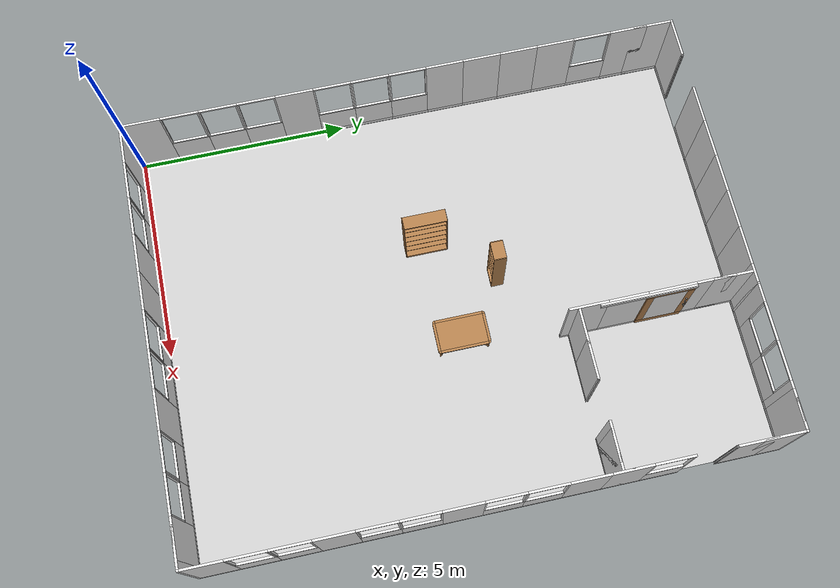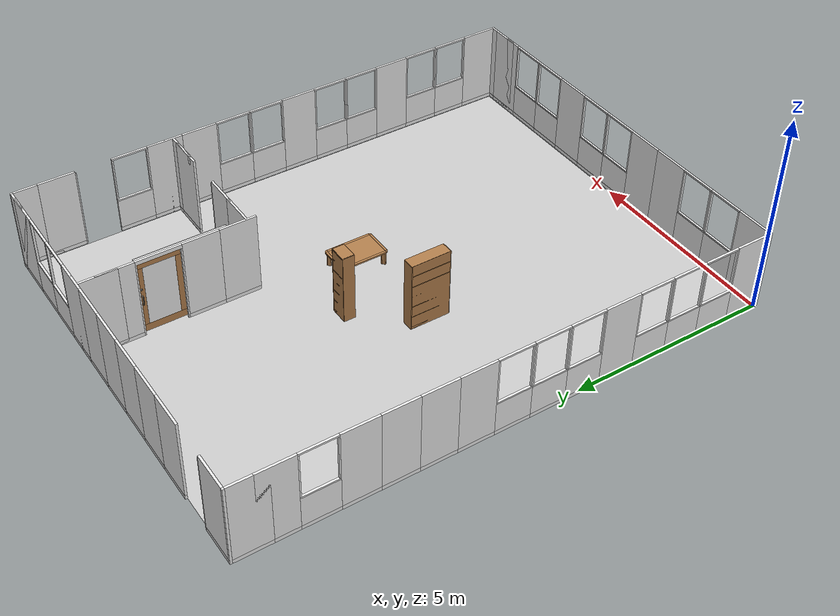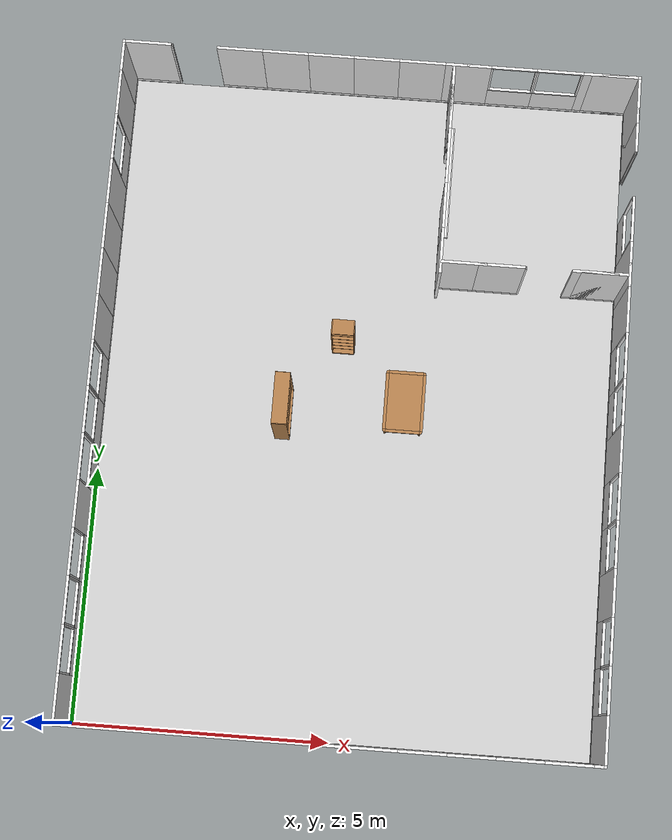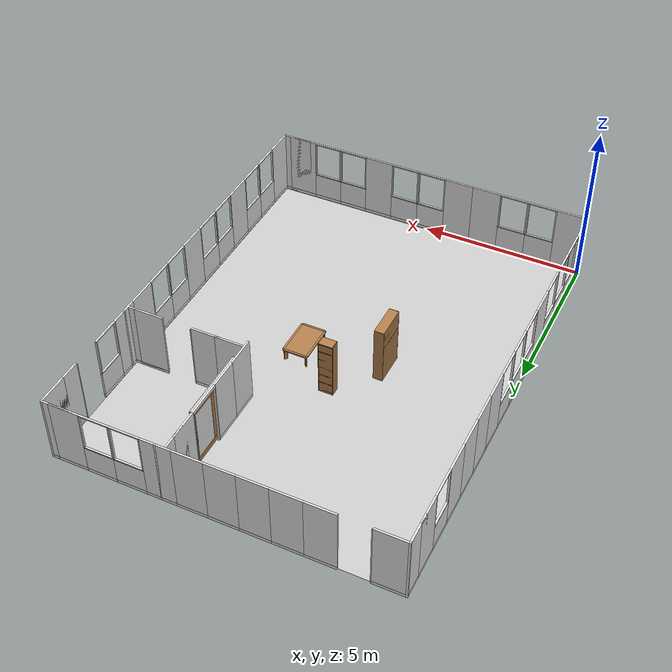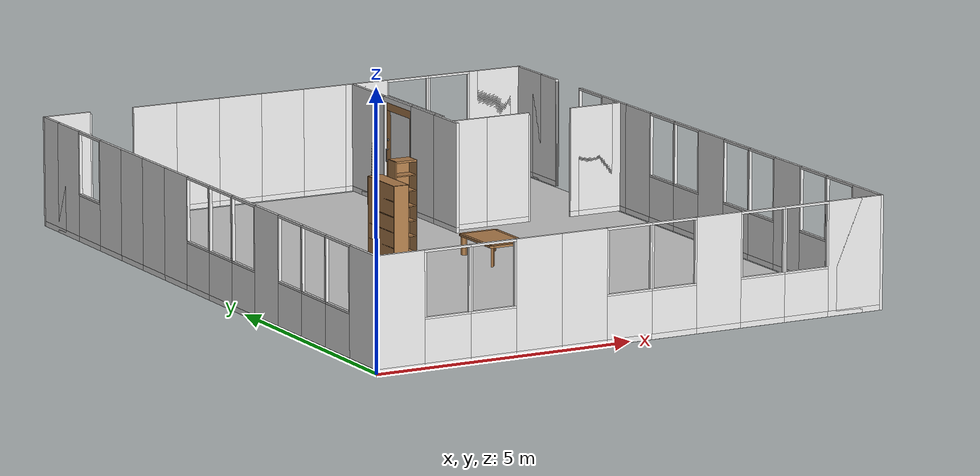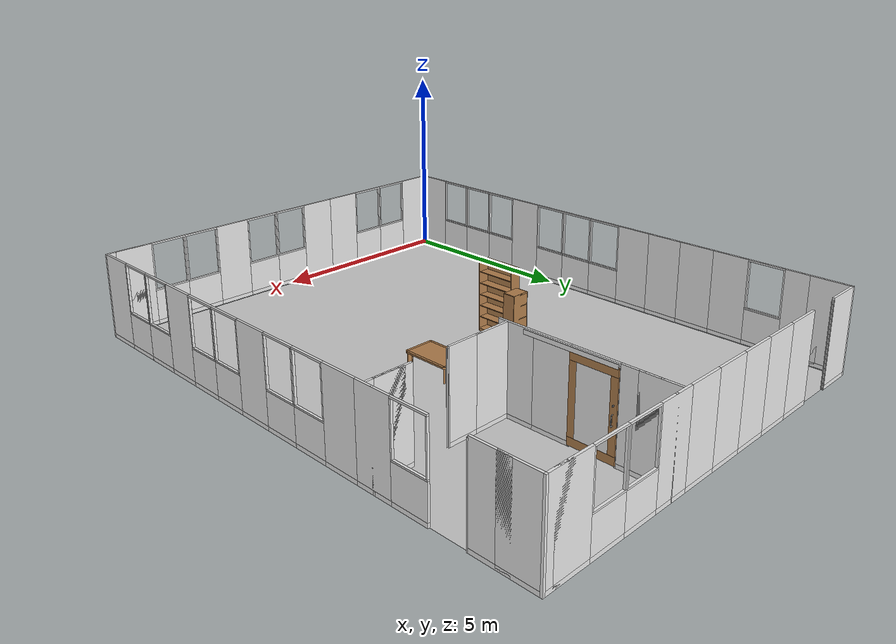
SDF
<sdf version="1.4">
 <world name="apartment">
  <scene>
   <ambient>0.5 0.5 0.5 1</ambient>
   <shadows>0</shadows>
   <grid>0</grid>
   <background>0.7 0.7 0.7 1</background>
  </scene>
  <physics type="ode">
   <gravity>0 0 -9.8</gravity>
   <max_step_size>0.001</max_step_size>
   <real_time_factor>1</real_time_factor>
   <real_time_update_rate>1000</real_time_update_rate>
  </physics>
  <model name="gplane">
   <pose>5.0375 6.59 0 0 -0 0</pose>
   <link name="body">
    <collision name="gplane_coll">
     <geometry><plane><normal>0 0 1</normal><size>10.075 13.18</size></plane></geometry>
     <surface><contact><ode><kp>1e+06</kp><kd>1</kd></ode></contact></surface>
     <laser_retro>2000</laser_retro>
    </collision>
    <visual name="gplane_vis">
     <geometry><plane><normal>0 0 1</normal><size>10.075 13.18</size></plane></geometry>
     <material>
      <script>
       <uri>model://base_materials/carpet/scripts</uri>
       <uri>model://base_materials/carpet/textures</uri>
       <name>carpet/carpet01</name>
      </script>
     </material>
     <cast_shadows>0</cast_shadows>
    </visual>
    <velocity_decay><linear>0</linear><angular>0</angular></velocity_decay>
   </link>
   <static>1</static>
  </model>
  <light name="inner_point_white1" type="point">
   <pose>4 5 4 0 -0 0</pose>
   <diffuse>0.2 0.2 0.2 1</diffuse>
   <specular>0.1 0.1 0.1 1</specular>
   <attenuation>
    <range>20</range>
    <linear>0.1</linear>
    <constant>0.2</constant>
    <quadratic>0</quadratic>
   </attenuation>
   <cast_shadows>0</cast_shadows>
   <direction>0 0 -1</direction>
  </light>
  <light name="inner_point_white2" type="point">
   <pose>4 10 4 0 -0 0</pose>
   <diffuse>0.2 0.2 0.2 1</diffuse>
   <specular>0.1 0.1 0.1 1</specular>
   <attenuation>
    <range>20</range>
    <linear>0.1</linear>
    <constant>0.2</constant>
    <quadratic>0</quadratic>
   </attenuation>
   <cast_shadows>0</cast_shadows>
   <direction>0 0 -1</direction>
  </light>
  <light name="inner_point_white3" type="point">
   <pose>8 5 4 0 -0 0</pose>
   <diffuse>0.2 0.2 0.2 1</diffuse>
   <specular>0.1 0.1 0.1 1</specular>
   <attenuation>
    <range>20</range>
    <linear>0.1</linear>
    <constant>0.2</constant>
    <quadratic>0</quadratic>
   </attenuation>
   <cast_shadows>0</cast_shadows>
   <direction>0 0 -1</direction>
  </light>
  <light name="inner_point_white4" type="point">
   <pose>8 10 4 0 -0 0</pose>
   <diffuse>0.2 0.2 0.2 1</diffuse>
   <specular>0.1 0.1 0.1 1</specular>
   <attenuation>
    <range>20</range>
    <linear>0.1</linear>
    <constant>0.2</constant>
    <quadratic>0</quadratic>
   </attenuation>
   <cast_shadows>0</cast_shadows>
   <direction>0 0 -1</direction>
  </light>
  <model name="wall_x00y00">
   <link name="link">
    <inertial>
     <mass>50</mass>
     <inertia><ixx>1</ixx><ixy>0</ixy><ixz>0</ixz><iyy>1</iyy><iyz>0</iyz><izz>1</izz></inertia>
    </inertial>
    <visual name="_frame">
     <pose>0 0 1.045 0 -0 0</pose>
     <geometry><box><size>0.055 0.055 2.09</size></box></geometry>
     <material>
      <script><uri>model://base_materials/color/scripts</uri><name>hsr_color/white</name></script>
     </material>
    </visual>
    <collision name="collision_frame">
     <pose>0 0 1.045 0 -0 0</pose>
     <geometry><box><size>0.055 0.055 2.09</size></box></geometry>
    </collision>
    <velocity_decay><linear>0</linear><angular>0</angular></velocity_decay>
   </link>
   <static>1</static>
   <pose>-0.0275 -0.0275 0 0 -0 0</pose>
  </model>
  <model name="wall_x00y01">
   <link name="link">
    <inertial>
     <mass>50</mass>
     <inertia><ixx>1</ixx><ixy>0</ixy><ixz>0</ixz><iyy>1</iyy><iyz>0</iyz><izz>1</izz></inertia>
    </inertial>
    <visual name="bottom_frame">
     <pose>0 0 0.05 0 -0 0</pose>
     <geometry><box><size>0.055 0.9 0.1</size></box></geometry>
     <material>
      <script><uri>model://base_materials/color/scripts</uri><name>hsr_color/white</name></script>
     </material>
    </visual>
    <collision name="collision_bottom_frame">
     <pose>0 0 0.05 0 -0 0</pose>
     <geometry><box><size>0.055 0.9 0.1</size></box></geometry>
    </collision>
    <visual name="wall">
     <pose>0 0 1.095 0 -0 0</pose>
     <geometry><box><size>0.055 0.9 1.99</size></box></geometry>
     <material>
      <script>
       <uri>model://base_materials/wall/scripts</uri>
       <uri>model://base_materials/wall/textures</uri>
       <name>wall/white_noise</name>
      </script>
     </material>
    </visual>
    <collision name="collision_wall">
     <pose>0 0 1.095 0 -0 0</pose>
     <geometry><box><size>0.055 0.9 1.99</size></box></geometry>
    </collision>
    <velocity_decay><linear>0</linear><angular>0</angular></velocity_decay>
   </link>
   <static>1</static>
   <pose>-0.0275 0.45 0 0 -0 0</pose>
  </model>
  <model name="wall_x00y02">
   <link name="link">
    <inertial>
     <mass>50</mass>
     <inertia><ixx>1</ixx><ixy>0</ixy><ixz>0</ixz><iyy>1</iyy><iyz>0</iyz><izz>1</izz></inertia>
    </inertial>
    <visual name="bottom_frame">
     <pose>0 0 0.05 0 -0 0</pose>
     <geometry><box><size>0.055 0.9 0.1</size></box></geometry>
     <material>
      <script><uri>model://base_materials/color/scripts</uri><name>hsr_color/white</name></script>
     </material>
    </visual>
    <collision name="collision_bottom_frame">
     <pose>0 0 0.05 0 -0 0</pose>
     <geometry><box><size>0.055 0.9 0.1</size></box></geometry>
    </collision>
    <visual name="wall">
     <pose>0 0 0.4875 0 -0 0</pose>
     <geometry><box><size>0.055 0.9 0.775</size></box></geometry>
     <material>
      <script>
       <uri>model://base_materials/wall/scripts</uri>
       <uri>model://base_materials/wall/textures</uri>
       <name>wall/white_noise</name>
      </script>
     </material>
    </visual>
    <collision name="collision_wall">
     <pose>0 0 0.4875 0 -0 0</pose>
     <geometry><box><size>0.055 0.9 0.775</size></box></geometry>
    </collision>
    <visual name="center_frame">
     <pose>0 0 0.8925 0 -0 0</pose>
     <geometry><box><size>0.055 0.9 0.035</size></box></geometry>
     <material>
      <script><uri>model://base_materials/color/scripts</uri><name>hsr_color/white</name></script>
     </material>
    </visual>
    <collision name="collision_center_frame">
     <pose>0 0 0.8925 0 -0 0</pose>
     <geometry><box><size>0.055 0.9 0.035</size></box></geometry>
    </collision>
    <visual name="right_frame">
     <pose>0 0.4325 1.48 0 -0 0</pose>
     <geometry><box><size>0.055 0.035 1.14</size></box></geometry>
     <material>
      <script><uri>model://base_materials/color/scripts</uri><name>hsr_color/white</name></script>
     </material>
    </visual>
    <collision name="collision_right_frame">
     <pose>0 0.4325 1.48 0 -0 0</pose>
     <geometry><box><size>0.055 0.035 1.14</size></box></geometry>
    </collision>
    <visual name="left_frame">
     <pose>0 -0.4325 1.48 0 -0 0</pose>
     <geometry><box><size>0.055 0.035 1.14</size></box></geometry>
     <material>
      <script><uri>model://base_materials/color/scripts</uri><name>hsr_color/white</name></script>
     </material>
    </visual>
    <collision name="collision_left_frame">
     <pose>0 -0.4325 1.48 0 -0 0</pose>
     <geometry><box><size>0.055 0.035 1.14</size></box></geometry>
    </collision>
    <visual name="top_frame">
     <pose>0 0 2.07 0 -0 0</pose>
     <geometry><box><size>0.055 0.9 0.04</size></box></geometry>
     <material>
      <script><uri>model://base_materials/color/scripts</uri><name>hsr_color/white</name></script>
     </material>
    </visual>
    <collision name="collision_top_frame">
     <pose>0 0 2.07 0 -0 0</pose>
     <geometry><box><size>0.055 0.9 0.04</size></box></geometry>
    </collision>
    <velocity_decay><linear>0</linear><angular>0</angular></velocity_decay>
   </link>
   <static>1</static>
   <pose>-0.0275 1.35 0 0 -0 0</pose>
  </model>
  <model name="wall_x00y03">
   <link name="link">
    <inertial>
     <mass>50</mass>
     <inertia><ixx>1</ixx><ixy>0</ixy><ixz>0</ixz><iyy>1</iyy><iyz>0</iyz><izz>1</izz></inertia>
    </inertial>
    <visual name="bottom_frame">
     <pose>0 0 0.05 0 -0 0</pose>
     <geometry><box><size>0.055 0.9 0.1</size></box></geometry>
     <material>
      <script><uri>model://base_materials/color/scripts</uri><name>hsr_color/white</name></script>
     </material>
    </visual>
    <collision name="collision_bottom_frame">
     <pose>0 0 0.05 0 -0 0</pose>
     <geometry><box><size>0.055 0.9 0.1</size></box></geometry>
    </collision>
    <visual name="wall">
     <pose>0 0 0.4875 0 -0 0</pose>
     <geometry><box><size>0.055 0.9 0.775</size></box></geometry>
     <material>
      <script>
       <uri>model://base_materials/wall/scripts</uri>
       <uri>model://base_materials/wall/textures</uri>
       <name>wall/white_noise</name>
      </script>
     </material>
    </visual>
    <collision name="collision_wall">
     <pose>0 0 0.4875 0 -0 0</pose>
     <geometry><box><size>0.055 0.9 0.775</size></box></geometry>
    </collision>
    <visual name="center_frame">
     <pose>0 0 0.8925 0 -0 0</pose>
     <geometry><box><size>0.055 0.9 0.035</size></box></geometry>
     <material>
      <script><uri>model://base_materials/color/scripts</uri><name>hsr_color/white</name></script>
     </material>
    </visual>
    <collision name="collision_center_frame">
     <pose>0 0 0.8925 0 -0 0</pose>
     <geometry><box><size>0.055 0.9 0.035</size></box></geometry>
    </collision>
    <visual name="right_frame">
     <pose>0 0.4325 1.48 0 -0 0</pose>
     <geometry><box><size>0.055 0.035 1.14</size></box></geometry>
     <material>
      <script><uri>model://base_materials/color/scripts</uri><name>hsr_color/white</name></script>
     </material>
    </visual>
    <collision name="collision_right_frame">
     <pose>0 0.4325 1.48 0 -0 0</pose>
     <geometry><box><size>0.055 0.035 1.14</size></box></geometry>
    </collision>
    <visual name="left_frame">
     <pose>0 -0.4325 1.48 0 -0 0</pose>
     <geometry><box><size>0.055 0.035 1.14</size></box></geometry>
     <material>
      <script><uri>model://base_materials/color/scripts</uri><name>hsr_color/white</name></script>
     </material>
    </visual>
    <collision name="collision_left_frame">
     <pose>0 -0.4325 1.48 0 -0 0</pose>
     <geometry><box><size>0.055 0.035 1.14</size></box></geometry>
    </collision>
    <visual name="top_frame">
     <pose>0 0 2.07 0 -0 0</pose>
     <geometry><box><size>0.055 0.9 0.04</size></box></geometry>
     <material>
      <script><uri>model://base_materials/color/scripts</uri><name>hsr_color/white</name></script>
     </material>
    </visual>
    <collision name="collision_top_frame">
     <pose>0 0 2.07 0 -0 0</pose>
     <geometry><box><size>0.055 0.9 0.04</size></box></geometry>
    </collision>
    <velocity_decay><linear>0</linear><angular>0</angular></velocity_decay>
   </link>
   <static>1</static>
   <pose>-0.0275 2.25 0 0 -0 0</pose>
  </model>
  <model name="wall_x00y04">
   <link name="link">
    <inertial>
     <mass>50</mass>
     <inertia><ixx>1</ixx><ixy>0</ixy><ixz>0</ixz><iyy>1</iyy><iyz>0</iyz><izz>1</izz></inertia>
    </inertial>
    <visual name="bottom_frame">
     <pose>0 0 0.05 0 -0 0</pose>
     <geometry><box><size>0.055 0.9 0.1</size></box></geometry>
     <material>
      <script><uri>model://base_materials/color/scripts</uri><name>hsr_color/white</name></script>
     </material>
    </visual>
    <collision name="collision_bottom_frame">
     <pose>0 0 0.05 0 -0 0</pose>
     <geometry><box><size>0.055 0.9 0.1</size></box></geometry>
    </collision>
    <visual name="wall">
     <pose>0 0 0.4875 0 -0 0</pose>
     <geometry><box><size>0.055 0.9 0.775</size></box></geometry>
     <material>
      <script>
       <uri>model://base_materials/wall/scripts</uri>
       <uri>model://base_materials/wall/textures</uri>
       <name>wall/white_noise</name>
      </script>
     </material>
    </visual>
    <collision name="collision_wall">
     <pose>0 0 0.4875 0 -0 0</pose>
     <geometry><box><size>0.055 0.9 0.775</size></box></geometry>
    </collision>
    <visual name="center_frame">
     <pose>0 0 0.8925 0 -0 0</pose>
     <geometry><box><size>0.055 0.9 0.035</size></box></geometry>
     <material>
      <script><uri>model://base_materials/color/scripts</uri><name>hsr_color/white</name></script>
     </material>
    </visual>
    <collision name="collision_center_frame">
     <pose>0 0 0.8925 0 -0 0</pose>
     <geometry><box><size>0.055 0.9 0.035</size></box></geometry>
    </collision>
    <visual name="right_frame">
     <pose>0 0.4325 1.48 0 -0 0</pose>
     <geometry><box><size>0.055 0.035 1.14</size></box></geometry>
     <material>
      <script><uri>model://base_materials/color/scripts</uri><name>hsr_color/white</name></script>
     </material>
    </visual>
    <collision name="collision_right_frame">
     <pose>0 0.4325 1.48 0 -0 0</pose>
     <geometry><box><size>0.055 0.035 1.14</size></box></geometry>
    </collision>
    <visual name="left_frame">
     <pose>0 -0.4325 1.48 0 -0 0</pose>
     <geometry><box><size>0.055 0.035 1.14</size></box></geometry>
     <material>
      <script><uri>model://base_materials/color/scripts</uri><name>hsr_color/white</name></script>
     </material>
    </visual>
    <collision name="collision_left_frame">
     <pose>0 -0.4325 1.48 0 -0 0</pose>
     <geometry><box><size>0.055 0.035 1.14</size></box></geometry>
    </collision>
    <visual name="top_frame">
     <pose>0 0 2.07 0 -0 0</pose>
     <geometry><box><size>0.055 0.9 0.04</size></box></geometry>
     <material>
      <script><uri>model://base_materials/color/scripts</uri><name>hsr_color/white</name></script>
     </material>
    </visual>
    <collision name="collision_top_frame">
     <pose>0 0 2.07 0 -0 0</pose>
     <geometry><box><size>0.055 0.9 0.04</size></box></geometry>
    </collision>
    <velocity_decay><linear>0</linear><angular>0</angular></velocity_decay>
   </link>
   <static>1</static>
   <pose>-0.0275 3.15 0 0 -0 0</pose>
  </model>
  <model name="wall_x00y05">
   <link name="link">
    <inertial>
     <mass>50</mass>
     <inertia><ixx>1</ixx><ixy>0</ixy><ixz>0</ixz><iyy>1</iyy><iyz>0</iyz><izz>1</izz></inertia>
    </inertial>
    <visual name="bottom_frame">
     <pose>0 0 0.05 0 -0 0</pose>
     <geometry><box><size>0.055 0.9 0.1</size></box></geometry>
     <material>
      <script><uri>model://base_materials/color/scripts</uri><name>hsr_color/white</name></script>
     </material>
    </visual>
    <collision name="collision_bottom_frame">
     <pose>0 0 0.05 0 -0 0</pose>
     <geometry><box><size>0.055 0.9 0.1</size></box></geometry>
    </collision>
    <visual name="wall">
     <pose>0 0 1.095 0 -0 0</pose>
     <geometry><box><size>0.055 0.9 1.99</size></box></geometry>
     <material>
      <script>
       <uri>model://base_materials/wall/scripts</uri>
       <uri>model://base_materials/wall/textures</uri>
       <name>wall/white_noise</name>
      </script>
     </material>
    </visual>
    <collision name="collision_wall">
     <pose>0 0 1.095 0 -0 0</pose>
     <geometry><box><size>0.055 0.9 1.99</size></box></geometry>
    </collision>
    <velocity_decay><linear>0</linear><angular>0</angular></velocity_decay>
   </link>
   <static>1</static>
   <pose>-0.0275 4.05 0 0 -0 0</pose>
  </model>
  <model name="wall_x00y06">
   <link name="link">
    <inertial>
     <mass>50</mass>
     <inertia><ixx>1</ixx><ixy>0</ixy><ixz>0</ixz><iyy>1</iyy><iyz>0</iyz><izz>1</izz></inertia>
    </inertial>
    <visual name="bottom_frame">
     <pose>0 0 0.05 0 -0 0</pose>
     <geometry><box><size>0.055 0.9 0.1</size></box></geometry>
     <material>
      <script><uri>model://base_materials/color/scripts</uri><name>hsr_color/white</name></script>
     </material>
    </visual>
    <collision name="collision_bottom_frame">
     <pose>0 0 0.05 0 -0 0</pose>
     <geometry><box><size>0.055 0.9 0.1</size></box></geometry>
    </collision>
    <visual name="wall">
     <pose>0 0 0.4875 0 -0 0</pose>
     <geometry><box><size>0.055 0.9 0.775</size></box></geometry>
     <material>
      <script>
       <uri>model://base_materials/wall/scripts</uri>
       <uri>model://base_materials/wall/textures</uri>
       <name>wall/white_noise</name>
      </script>
     </material>
    </visual>
    <collision name="collision_wall">
     <pose>0 0 0.4875 0 -0 0</pose>
     <geometry><box><size>0.055 0.9 0.775</size></box></geometry>
    </collision>
    <visual name="center_frame">
     <pose>0 0 0.8925 0 -0 0</pose>
     <geometry><box><size>0.055 0.9 0.035</size></box></geometry>
     <material>
      <script><uri>model://base_materials/color/scripts</uri><name>hsr_color/white</name></script>
     </material>
    </visual>
    <collision name="collision_center_frame">
     <pose>0 0 0.8925 0 -0 0</pose>
     <geometry><box><size>0.055 0.9 0.035</size></box></geometry>
    </collision>
    <visual name="right_frame">
     <pose>0 0.4325 1.48 0 -0 0</pose>
     <geometry><box><size>0.055 0.035 1.14</size></box></geometry>
     <material>
      <script><uri>model://base_materials/color/scripts</uri><name>hsr_color/white</name></script>
     </material>
    </visual>
    <collision name="collision_right_frame">
     <pose>0 0.4325 1.48 0 -0 0</pose>
     <geometry><box><size>0.055 0.035 1.14</size></box></geometry>
    </collision>
    <visual name="left_frame">
     <pose>0 -0.4325 1.48 0 -0 0</pose>
     <geometry><box><size>0.055 0.035 1.14</size></box></geometry>
     <material>
      <script><uri>model://base_materials/color/scripts</uri><name>hsr_color/white</name></script>
     </material>
    </visual>
    <collision name="collision_left_frame">
     <pose>0 -0.4325 1.48 0 -0 0</pose>
     <geometry><box><size>0.055 0.035 1.14</size></box></geometry>
    </collision>
    <visual name="top_frame">
     <pose>0 0 2.07 0 -0 0</pose>
     <geometry><box><size>0.055 0.9 0.04</size></box></geometry>
     <material>
      <script><uri>model://base_materials/color/scripts</uri><name>hsr_color/white</name></script>
     </material>
    </visual>
    <collision name="collision_top_frame">
     <pose>0 0 2.07 0 -0 0</pose>
     <geometry><box><size>0.055 0.9 0.04</size></box></geometry>
    </collision>
    <velocity_decay><linear>0</linear><angular>0</angular></velocity_decay>
   </link>
   <static>1</static>
   <pose>-0.0275 4.95 0 0 -0 0</pose>
  </model>
  <model name="wall_x00y07">
   <link name="link">
    <inertial>
     <mass>50</mass>
     <inertia><ixx>1</ixx><ixy>0</ixy><ixz>0</ixz><iyy>1</iyy><iyz>0</iyz><izz>1</izz></inertia>
    </inertial>
    <visual name="bottom_frame">
     <pose>0 0 0.05 0 -0 0</pose>
     <geometry><box><size>0.055 0.9 0.1</size></box></geometry>
     <material>
      <script><uri>model://base_materials/color/scripts</uri><name>hsr_color/white</name></script>
     </material>
    </visual>
    <collision name="collision_bottom_frame">
     <pose>0 0 0.05 0 -0 0</pose>
     <geometry><box><size>0.055 0.9 0.1</size></box></geometry>
    </collision>
    <visual name="wall">
     <pose>0 0 0.4875 0 -0 0</pose>
     <geometry><box><size>0.055 0.9 0.775</size></box></geometry>
     <material>
      <script>
       <uri>model://base_materials/wall/scripts</uri>
       <uri>model://base_materials/wall/textures</uri>
       <name>wall/white_noise</name>
      </script>
     </material>
    </visual>
    <collision name="collision_wall">
     <pose>0 0 0.4875 0 -0 0</pose>
     <geometry><box><size>0.055 0.9 0.775</size></box></geometry>
    </collision>
    <visual name="center_frame">
     <pose>0 0 0.8925 0 -0 0</pose>
     <geometry><box><size>0.055 0.9 0.035</size></box></geometry>
     <material>
      <script><uri>model://base_materials/color/scripts</uri><name>hsr_color/white</name></script>
     </material>
    </visual>
    <collision name="collision_center_frame">
     <pose>0 0 0.8925 0 -0 0</pose>
     <geometry><box><size>0.055 0.9 0.035</size></box></geometry>
    </collision>
    <visual name="right_frame">
     <pose>0 0.4325 1.48 0 -0 0</pose>
     <geometry><box><size>0.055 0.035 1.14</size></box></geometry>
     <material>
      <script><uri>model://base_materials/color/scripts</uri><name>hsr_color/white</name></script>
     </material>
    </visual>
    <collision name="collision_right_frame">
     <pose>0 0.4325 1.48 0 -0 0</pose>
     <geometry><box><size>0.055 0.035 1.14</size></box></geometry>
    </collision>
    <visual name="left_frame">
     <pose>0 -0.4325 1.48 0 -0 0</pose>
     <geometry><box><size>0.055 0.035 1.14</size></box></geometry>
     <material>
      <script><uri>model://base_materials/color/scripts</uri><name>hsr_color/white</name></script>
     </material>
    </visual>
    <collision name="collision_left_frame">
     <pose>0 -0.4325 1.48 0 -0 0</pose>
     <geometry><box><size>0.055 0.035 1.14</size></box></geometry>
    </collision>
    <visual name="top_frame">
     <pose>0 0 2.07 0 -0 0</pose>
     <geometry><box><size>0.055 0.9 0.04</size></box></geometry>
     <material>
      <script><uri>model://base_materials/color/scripts</uri><name>hsr_color/white</name></script>
     </material>
    </visual>
    <collision name="collision_top_frame">
     <pose>0 0 2.07 0 -0 0</pose>
     <geometry><box><size>0.055 0.9 0.04</size></box></geometry>
    </collision>
    <velocity_decay><linear>0</linear><angular>0</angular></velocity_decay>
   </link>
   <static>1</static>
   <pose>-0.0275 5.85 0 0 -0 0</pose>
  </model>
  <model name="wall_x00y08">
   <link name="link">
    <inertial>
     <mass>50</mass>
     <inertia><ixx>1</ixx><ixy>0</ixy><ixz>0</ixz><iyy>1</iyy><iyz>0</iyz><izz>1</izz></inertia>
    </inertial>
    <visual name="bottom_frame">
     <pose>0 0 0.05 0 -0 0</pose>
     <geometry><box><size>0.055 0.9 0.1</size></box></geometry>
     <material>
      <script><uri>model://base_materials/color/scripts</uri><name>hsr_color/white</name></script>
     </material>
    </visual>
    <collision name="collision_bottom_frame">
     <pose>0 0 0.05 0 -0 0</pose>
     <geometry><box><size>0.055 0.9 0.1</size></box></geometry>
    </collision>
    <visual name="wall">
     <pose>0 0 0.4875 0 -0 0</pose>
     <geometry><box><size>0.055 0.9 0.775</size></box></geometry>
     <material>
      <script>
       <uri>model://base_materials/wall/scripts</uri>
       <uri>model://base_materials/wall/textures</uri>
       <name>wall/white_noise</name>
      </script>
     </material>
    </visual>
    <collision name="collision_wall">
     <pose>0 0 0.4875 0 -0 0</pose>
     <geometry><box><size>0.055 0.9 0.775</size></box></geometry>
    </collision>
    <visual name="center_frame">
     <pose>0 0 0.8925 0 -0 0</pose>
     <geometry><box><size>0.055 0.9 0.035</size></box></geometry>
     <material>
      <script><uri>model://base_materials/color/scripts</uri><name>hsr_color/white</name></script>
     </material>
    </visual>
    <collision name="collision_center_frame">
     <pose>0 0 0.8925 0 -0 0</pose>
     <geometry><box><size>0.055 0.9 0.035</size></box></geometry>
    </collision>
    <visual name="right_frame">
     <pose>0 0.4325 1.48 0 -0 0</pose>
     <geometry><box><size>0.055 0.035 1.14</size></box></geometry>
     <material>
      <script><uri>model://base_materials/color/scripts</uri><name>hsr_color/white</name></script>
     </material>
    </visual>
    <collision name="collision_right_frame">
     <pose>0 0.4325 1.48 0 -0 0</pose>
     <geometry><box><size>0.055 0.035 1.14</size></box></geometry>
    </collision>
    <visual name="left_frame">
     <pose>0 -0.4325 1.48 0 -0 0</pose>
     <geometry><box><size>0.055 0.035 1.14</size></box></geometry>
     <material>
      <script><uri>model://base_materials/color/scripts</uri><name>hsr_color/white</name></script>
     </material>
    </visual>
    <collision name="collision_left_frame">
     <pose>0 -0.4325 1.48 0 -0 0</pose>
     <geometry><box><size>0.055 0.035 1.14</size></box></geometry>
    </collision>
    <visual name="top_frame">
     <pose>0 0 2.07 0 -0 0</pose>
     <geometry><box><size>0.055 0.9 0.04</size></box></geometry>
     <material>
      <script><uri>model://base_materials/color/scripts</uri><name>hsr_color/white</name></script>
     </material>
    </visual>
    <collision name="collision_top_frame">
     <pose>0 0 2.07 0 -0 0</pose>
     <geometry><box><size>0.055 0.9 0.04</size></box></geometry>
    </collision>
    <velocity_decay><linear>0</linear><angular>0</angular></velocity_decay>
   </link>
   <static>1</static>
   <pose>-0.0275 6.75 0 0 -0 0</pose>
  </model>
  <model name="wall_x00y09">
   <link name="link">
    <inertial>
     <mass>50</mass>
     <inertia><ixx>1</ixx><ixy>0</ixy><ixz>0</ixz><iyy>1</iyy><iyz>0</iyz><izz>1</izz></inertia>
    </inertial>
    <visual name="bottom_frame">
     <pose>0 0 0.05 0 -0 0</pose>
     <geometry><box><size>0.055 0.9 0.1</size></box></geometry>
     <material>
      <script><uri>model://base_materials/color/scripts</uri><name>hsr_color/white</name></script>
     </material>
    </visual>
    <collision name="collision_bottom_frame">
     <pose>0 0 0.05 0 -0 0</pose>
     <geometry><box><size>0.055 0.9 0.1</size></box></geometry>
    </collision>
    <visual name="wall">
     <pose>0 0 1.095 0 -0 0</pose>
     <geometry><box><size>0.055 0.9 1.99</size></box></geometry>
     <material>
      <script>
       <uri>model://base_materials/wall/scripts</uri>
       <uri>model://base_materials/wall/textures</uri>
       <name>wall/white_noise</name>
      </script>
     </material>
    </visual>
    <collision name="collision_wall">
     <pose>0 0 1.095 0 -0 0</pose>
     <geometry><box><size>0.055 0.9 1.99</size></box></geometry>
    </collision>
    <velocity_decay><linear>0</linear><angular>0</angular></velocity_decay>
   </link>
   <static>1</static>
   <pose>-0.0275 7.65 0 0 -0 0</pose>
  </model>
  <model name="wall_x00y10">
   <link name="link">
    <inertial>
     <mass>50</mass>
     <inertia><ixx>1</ixx><ixy>0</ixy><ixz>0</ixz><iyy>1</iyy><iyz>0</iyz><izz>1</izz></inertia>
    </inertial>
    <visual name="bottom_frame">
     <pose>0 0 0.05 0 -0 0</pose>
     <geometry><box><size>0.055 0.9 0.1</size></box></geometry>
     <material>
      <script><uri>model://base_materials/color/scripts</uri><name>hsr_color/white</name></script>
     </material>
    </visual>
    <collision name="collision_bottom_frame">
     <pose>0 0 0.05 0 -0 0</pose>
     <geometry><box><size>0.055 0.9 0.1</size></box></geometry>
    </collision>
    <visual name="wall">
     <pose>0 0 1.095 0 -0 0</pose>
     <geometry><box><size>0.055 0.9 1.99</size></box></geometry>
     <material>
      <script>
       <uri>model://base_materials/wall/scripts</uri>
       <uri>model://base_materials/wall/textures</uri>
       <name>wall/white_noise</name>
      </script>
     </material>
    </visual>
    <collision name="collision_wall">
     <pose>0 0 1.095 0 -0 0</pose>
     <geometry><box><size>0.055 0.9 1.99</size></box></geometry>
    </collision>
    <velocity_decay><linear>0</linear><angular>0</angular></velocity_decay>
   </link>
   <static>1</static>
   <pose>-0.0275 8.55 0 0 -0 0</pose>
  </model>
  <model name="wall_x00y11">
   <link name="link">
    <inertial>
     <mass>50</mass>
     <inertia><ixx>1</ixx><ixy>0</ixy><ixz>0</ixz><iyy>1</iyy><iyz>0</iyz><izz>1</izz></inertia>
    </inertial>
    <visual name="bottom_frame">
     <pose>0 0 0.05 0 -0 0</pose>
     <geometry><box><size>0.055 0.9 0.1</size></box></geometry>
     <material>
      <script><uri>model://base_materials/color/scripts</uri><name>hsr_color/white</name></script>
     </material>
    </visual>
    <collision name="collision_bottom_frame">
     <pose>0 0 0.05 0 -0 0</pose>
     <geometry><box><size>0.055 0.9 0.1</size></box></geometry>
    </collision>
    <visual name="wall">
     <pose>0 0 1.095 0 -0 0</pose>
     <geometry><box><size>0.055 0.9 1.99</size></box></geometry>
     <material>
      <script>
       <uri>model://base_materials/wall/scripts</uri>
       <uri>model://base_materials/wall/textures</uri>
       <name>wall/white_noise</name>
      </script>
     </material>
    </visual>
    <collision name="collision_wall">
     <pose>0 0 1.095 0 -0 0</pose>
     <geometry><box><size>0.055 0.9 1.99</size></box></geometry>
    </collision>
    <velocity_decay><linear>0</linear><angular>0</angular></velocity_decay>
   </link>
   <static>1</static>
   <pose>-0.0275 9.45 0 0 -0 0</pose>
  </model>
  <model name="wall_x00y12">
   <link name="link">
    <inertial>
     <mass>50</mass>
     <inertia><ixx>1</ixx><ixy>0</ixy><ixz>0</ixz><iyy>1</iyy><iyz>0</iyz><izz>1</izz></inertia>
    </inertial>
    <visual name="bottom_frame">
     <pose>0 0 0.05 0 -0 0</pose>
     <geometry><box><size>0.055 0.9 0.1</size></box></geometry>
     <material>
      <script><uri>model://base_materials/color/scripts</uri><name>hsr_color/white</name></script>
     </material>
    </visual>
    <collision name="collision_bottom_frame">
     <pose>0 0 0.05 0 -0 0</pose>
     <geometry><box><size>0.055 0.9 0.1</size></box></geometry>
    </collision>
    <visual name="wall">
     <pose>0 0 1.095 0 -0 0</pose>
     <geometry><box><size>0.055 0.9 1.99</size></box></geometry>
     <material>
      <script>
       <uri>model://base_materials/wall/scripts</uri>
       <uri>model://base_materials/wall/textures</uri>
       <name>wall/white_noise</name>
      </script>
     </material>
    </visual>
    <collision name="collision_wall">
     <pose>0 0 1.095 0 -0 0</pose>
     <geometry><box><size>0.055 0.9 1.99</size></box></geometry>
    </collision>
    <velocity_decay><linear>0</linear><angular>0</angular></velocity_decay>
   </link>
   <static>1</static>
   <pose>-0.0275 10.35 0 0 -0 0</pose>
  </model>
  <model name="wall_x00y13">
   <link name="link">
    <inertial>
     <mass>50</mass>
     <inertia><ixx>1</ixx><ixy>0</ixy><ixz>0</ixz><iyy>1</iyy><iyz>0</iyz><izz>1</izz></inertia>
    </inertial>
    <visual name="bottom_frame">
     <pose>0 0 0.05 0 -0 0</pose>
     <geometry><box><size>0.055 0.9 0.1</size></box></geometry>
     <material>
      <script><uri>model://base_materials/color/scripts</uri><name>hsr_color/white</name></script>
     </material>
    </visual>
    <collision name="collision_bottom_frame">
     <pose>0 0 0.05 0 -0 0</pose>
     <geometry><box><size>0.055 0.9 0.1</size></box></geometry>
    </collision>
    <visual name="wall">
     <pose>0 0 0.4875 0 -0 0</pose>
     <geometry><box><size>0.055 0.9 0.775</size></box></geometry>
     <material>
      <script>
       <uri>model://base_materials/wall/scripts</uri>
       <uri>model://base_materials/wall/textures</uri>
       <name>wall/white_noise</name>
      </script>
     </material>
    </visual>
    <collision name="collision_wall">
     <pose>0 0 0.4875 0 -0 0</pose>
     <geometry><box><size>0.055 0.9 0.775</size></box></geometry>
    </collision>
    <visual name="center_frame">
     <pose>0 0 0.8925 0 -0 0</pose>
     <geometry><box><size>0.055 0.9 0.035</size></box></geometry>
     <material>
      <script><uri>model://base_materials/color/scripts</uri><name>hsr_color/white</name></script>
     </material>
    </visual>
    <collision name="collision_center_frame">
     <pose>0 0 0.8925 0 -0 0</pose>
     <geometry><box><size>0.055 0.9 0.035</size></box></geometry>
    </collision>
    <visual name="right_frame">
     <pose>0 0.4325 1.48 0 -0 0</pose>
     <geometry><box><size>0.055 0.035 1.14</size></box></geometry>
     <material>
      <script><uri>model://base_materials/color/scripts</uri><name>hsr_color/white</name></script>
     </material>
    </visual>
    <collision name="collision_right_frame">
     <pose>0 0.4325 1.48 0 -0 0</pose>
     <geometry><box><size>0.055 0.035 1.14</size></box></geometry>
    </collision>
    <visual name="left_frame">
     <pose>0 -0.4325 1.48 0 -0 0</pose>
     <geometry><box><size>0.055 0.035 1.14</size></box></geometry>
     <material>
      <script><uri>model://base_materials/color/scripts</uri><name>hsr_color/white</name></script>
     </material>
    </visual>
    <collision name="collision_left_frame">
     <pose>0 -0.4325 1.48 0 -0 0</pose>
     <geometry><box><size>0.055 0.035 1.14</size></box></geometry>
    </collision>
    <visual name="top_frame">
     <pose>0 0 2.07 0 -0 0</pose>
     <geometry><box><size>0.055 0.9 0.04</size></box></geometry>
     <material>
      <script><uri>model://base_materials/color/scripts</uri><name>hsr_color/white</name></script>
     </material>
    </visual>
    <collision name="collision_top_frame">
     <pose>0 0 2.07 0 -0 0</pose>
     <geometry><box><size>0.055 0.9 0.04</size></box></geometry>
    </collision>
    <velocity_decay><linear>0</linear><angular>0</angular></velocity_decay>
   </link>
   <static>1</static>
   <pose>-0.0275 11.25 0 0 -0 0</pose>
  </model>
  <model name="wall_x00y14">
   <link name="link">
    <inertial>
     <mass>50</mass>
     <inertia><ixx>1</ixx><ixy>0</ixy><ixz>0</ixz><iyy>1</iyy><iyz>0</iyz><izz>1</izz></inertia>
    </inertial>
    <visual name="bottom_frame">
     <pose>0 0 0.05 0 -0 0</pose>
     <geometry><box><size>0.055 0.9 0.1</size></box></geometry>
     <material>
      <script><uri>model://base_materials/color/scripts</uri><name>hsr_color/white</name></script>
     </material>
    </visual>
    <collision name="collision_bottom_frame">
     <pose>0 0 0.05 0 -0 0</pose>
     <geometry><box><size>0.055 0.9 0.1</size></box></geometry>
    </collision>
    <visual name="wall">
     <pose>0 0 1.095 0 -0 0</pose>
     <geometry><box><size>0.055 0.9 1.99</size></box></geometry>
     <material>
      <script>
       <uri>model://base_materials/wall/scripts</uri>
       <uri>model://base_materials/wall/textures</uri>
       <name>wall/white_noise</name>
      </script>
     </material>
    </visual>
    <collision name="collision_wall">
     <pose>0 0 1.095 0 -0 0</pose>
     <geometry><box><size>0.055 0.9 1.99</size></box></geometry>
    </collision>
    <velocity_decay><linear>0</linear><angular>0</angular></velocity_decay>
   </link>
   <static>1</static>
   <pose>-0.0275 12.15 0 0 -0 0</pose>
  </model>
  <model name="wall_x00y15">
   <link name="link">
    <inertial>
     <mass>50</mass>
     <inertia><ixx>1</ixx><ixy>0</ixy><ixz>0</ixz><iyy>1</iyy><iyz>0</iyz><izz>1</izz></inertia>
    </inertial>
    <visual name="bottom_frame">
     <pose>0 0 0.05 0 -0 0</pose>
     <geometry><box><size>0.055 0.9 0.1</size></box></geometry>
     <material>
      <script><uri>model://base_materials/color/scripts</uri><name>hsr_color/white</name></script>
     </material>
    </visual>
    <collision name="collision_bottom_frame">
     <pose>0 0 0.05 0 -0 0</pose>
     <geometry><box><size>0.055 0.9 0.1</size></box></geometry>
    </collision>
    <visual name="wall">
     <pose>0 0 1.095 0 -0 0</pose>
     <geometry><box><size>0.055 0.9 1.99</size></box></geometry>
     <material>
      <script>
       <uri>model://base_materials/wall/scripts</uri>
       <uri>model://base_materials/wall/textures</uri>
       <name>wall/white_noise</name>
      </script>
     </material>
    </visual>
    <collision name="collision_wall">
     <pose>0 0 1.095 0 -0 0</pose>
     <geometry><box><size>0.055 0.9 1.99</size></box></geometry>
    </collision>
    <velocity_decay><linear>0</linear><angular>0</angular></velocity_decay>
   </link>
   <static>1</static>
   <pose>-0.0275 12.73 0 0 -0 0</pose>
  </model>
  <model name="wall_x00y16">
   <link name="link">
    <inertial>
     <mass>50</mass>
     <inertia><ixx>1</ixx><ixy>0</ixy><ixz>0</ixz><iyy>1</iyy><iyz>0</iyz><izz>1</izz></inertia>
    </inertial>
    <visual name="_frame">
     <pose>0 0 1.045 0 -0 0</pose>
     <geometry><box><size>0.055 0.055 2.09</size></box></geometry>
     <material>
      <script><uri>model://base_materials/color/scripts</uri><name>hsr_color/white</name></script>
     </material>
    </visual>
    <collision name="collision_frame">
     <pose>0 0 1.045 0 -0 0</pose>
     <geometry><box><size>0.055 0.055 2.09</size></box></geometry>
    </collision>
    <velocity_decay><linear>0</linear><angular>0</angular></velocity_decay>
   </link>
   <static>1</static>
   <pose>-0.0275 13.2075 0 0 -0 0</pose>
  </model>
  <model name="wall_x01y00">
   <link name="link">
    <inertial>
     <mass>50</mass>
     <inertia><ixx>1</ixx><ixy>0</ixy><ixz>0</ixz><iyy>1</iyy><iyz>0</iyz><izz>1</izz></inertia>
    </inertial>
    <visual name="bottom_frame">
     <pose>0 0 0.05 0 -0 0</pose>
     <geometry><box><size>0.055 0.9 0.1</size></box></geometry>
     <material>
      <script><uri>model://base_materials/color/scripts</uri><name>hsr_color/white</name></script>
     </material>
    </visual>
    <collision name="collision_bottom_frame">
     <pose>0 0 0.05 0 -0 0</pose>
     <geometry><box><size>0.055 0.9 0.1</size></box></geometry>
    </collision>
    <visual name="wall">
     <pose>0 0 1.095 0 -0 0</pose>
     <geometry><box><size>0.055 0.9 1.99</size></box></geometry>
     <material>
      <script>
       <uri>model://base_materials/wall/scripts</uri>
       <uri>model://base_materials/wall/textures</uri>
       <name>wall/white_noise</name>
      </script>
     </material>
    </visual>
    <collision name="collision_wall">
     <pose>0 0 1.095 0 -0 0</pose>
     <geometry><box><size>0.055 0.9 1.99</size></box></geometry>
    </collision>
    <velocity_decay><linear>0</linear><angular>0</angular></velocity_decay>
   </link>
   <static>1</static>
   <pose>0.45 -0.0275 0 0 -0 1.5708</pose>
  </model>
  <model name="wall_x02y00">
   <link name="link">
    <inertial>
     <mass>50</mass>
     <inertia><ixx>1</ixx><ixy>0</ixy><ixz>0</ixz><iyy>1</iyy><iyz>0</iyz><izz>1</izz></inertia>
    </inertial>
    <visual name="bottom_frame">
     <pose>0 0 0.05 0 -0 0</pose>
     <geometry><box><size>0.055 0.9 0.1</size></box></geometry>
     <material>
      <script><uri>model://base_materials/color/scripts</uri><name>hsr_color/white</name></script>
     </material>
    </visual>
    <collision name="collision_bottom_frame">
     <pose>0 0 0.05 0 -0 0</pose>
     <geometry><box><size>0.055 0.9 0.1</size></box></geometry>
    </collision>
    <visual name="wall">
     <pose>0 0 0.4875 0 -0 0</pose>
     <geometry><box><size>0.055 0.9 0.775</size></box></geometry>
     <material>
      <script>
       <uri>model://base_materials/wall/scripts</uri>
       <uri>model://base_materials/wall/textures</uri>
       <name>wall/white_noise</name>
      </script>
     </material>
    </visual>
    <collision name="collision_wall">
     <pose>0 0 0.4875 0 -0 0</pose>
     <geometry><box><size>0.055 0.9 0.775</size></box></geometry>
    </collision>
    <visual name="center_frame">
     <pose>0 0 0.8925 0 -0 0</pose>
     <geometry><box><size>0.055 0.9 0.035</size></box></geometry>
     <material>
      <script><uri>model://base_materials/color/scripts</uri><name>hsr_color/white</name></script>
     </material>
    </visual>
    <collision name="collision_center_frame">
     <pose>0 0 0.8925 0 -0 0</pose>
     <geometry><box><size>0.055 0.9 0.035</size></box></geometry>
    </collision>
    <visual name="right_frame">
     <pose>0 0.4325 1.48 0 -0 0</pose>
     <geometry><box><size>0.055 0.035 1.14</size></box></geometry>
     <material>
      <script><uri>model://base_materials/color/scripts</uri><name>hsr_color/white</name></script>
     </material>
    </visual>
    <collision name="collision_right_frame">
     <pose>0 0.4325 1.48 0 -0 0</pose>
     <geometry><box><size>0.055 0.035 1.14</size></box></geometry>
    </collision>
    <visual name="left_frame">
     <pose>0 -0.4325 1.48 0 -0 0</pose>
     <geometry><box><size>0.055 0.035 1.14</size></box></geometry>
     <material>
      <script><uri>model://base_materials/color/scripts</uri><name>hsr_color/white</name></script>
     </material>
    </visual>
    <collision name="collision_left_frame">
     <pose>0 -0.4325 1.48 0 -0 0</pose>
     <geometry><box><size>0.055 0.035 1.14</size></box></geometry>
    </collision>
    <visual name="top_frame">
     <pose>0 0 2.07 0 -0 0</pose>
     <geometry><box><size>0.055 0.9 0.04</size></box></geometry>
     <material>
      <script><uri>model://base_materials/color/scripts</uri><name>hsr_color/white</name></script>
     </material>
    </visual>
    <collision name="collision_top_frame">
     <pose>0 0 2.07 0 -0 0</pose>
     <geometry><box><size>0.055 0.9 0.04</size></box></geometry>
    </collision>
    <velocity_decay><linear>0</linear><angular>0</angular></velocity_decay>
   </link>
   <static>1</static>
   <pose>1.35 -0.0275 0 0 -0 1.5708</pose>
  </model>
  <model name="wall_x03y00">
   <link name="link">
    <inertial>
     <mass>50</mass>
     <inertia><ixx>1</ixx><ixy>0</ixy><ixz>0</ixz><iyy>1</iyy><iyz>0</iyz><izz>1</izz></inertia>
    </inertial>
    <visual name="bottom_frame">
     <pose>0 0 0.05 0 -0 0</pose>
     <geometry><box><size>0.055 0.9 0.1</size></box></geometry>
     <material>
      <script><uri>model://base_materials/color/scripts</uri><name>hsr_color/white</name></script>
     </material>
    </visual>
    <collision name="collision_bottom_frame">
     <pose>0 0 0.05 0 -0 0</pose>
     <geometry><box><size>0.055 0.9 0.1</size></box></geometry>
    </collision>
    <visual name="wall">
     <pose>0 0 0.4875 0 -0 0</pose>
     <geometry><box><size>0.055 0.9 0.775</size></box></geometry>
     <material>
      <script>
       <uri>model://base_materials/wall/scripts</uri>
       <uri>model://base_materials/wall/textures</uri>
       <name>wall/white_noise</name>
      </script>
     </material>
    </visual>
    <collision name="collision_wall">
     <pose>0 0 0.4875 0 -0 0</pose>
     <geometry><box><size>0.055 0.9 0.775</size></box></geometry>
    </collision>
    <visual name="center_frame">
     <pose>0 0 0.8925 0 -0 0</pose>
     <geometry><box><size>0.055 0.9 0.035</size></box></geometry>
     <material>
      <script><uri>model://base_materials/color/scripts</uri><name>hsr_color/white</name></script>
     </material>
    </visual>
    <collision name="collision_center_frame">
     <pose>0 0 0.8925 0 -0 0</pose>
     <geometry><box><size>0.055 0.9 0.035</size></box></geometry>
    </collision>
    <visual name="right_frame">
     <pose>0 0.4325 1.48 0 -0 0</pose>
     <geometry><box><size>0.055 0.035 1.14</size></box></geometry>
     <material>
      <script><uri>model://base_materials/color/scripts</uri><name>hsr_color/white</name></script>
     </material>
    </visual>
    <collision name="collision_right_frame">
     <pose>0 0.4325 1.48 0 -0 0</pose>
     <geometry><box><size>0.055 0.035 1.14</size></box></geometry>
    </collision>
    <visual name="left_frame">
     <pose>0 -0.4325 1.48 0 -0 0</pose>
     <geometry><box><size>0.055 0.035 1.14</size></box></geometry>
     <material>
      <script><uri>model://base_materials/color/scripts</uri><name>hsr_color/white</name></script>
     </material>
    </visual>
    <collision name="collision_left_frame">
     <pose>0 -0.4325 1.48 0 -0 0</pose>
     <geometry><box><size>0.055 0.035 1.14</size></box></geometry>
    </collision>
    <visual name="top_frame">
     <pose>0 0 2.07 0 -0 0</pose>
     <geometry><box><size>0.055 0.9 0.04</size></box></geometry>
     <material>
      <script><uri>model://base_materials/color/scripts</uri><name>hsr_color/white</name></script>
     </material>
    </visual>
    <collision name="collision_top_frame">
     <pose>0 0 2.07 0 -0 0</pose>
     <geometry><box><size>0.055 0.9 0.04</size></box></geometry>
    </collision>
    <velocity_decay><linear>0</linear><angular>0</angular></velocity_decay>
   </link>
   <static>1</static>
   <pose>2.25 -0.0275 0 0 -0 1.5708</pose>
  </model>
  <model name="wall_x04y00">
   <link name="link">
    <inertial>
     <mass>50</mass>
     <inertia><ixx>1</ixx><ixy>0</ixy><ixz>0</ixz><iyy>1</iyy><iyz>0</iyz><izz>1</izz></inertia>
    </inertial>
    <visual name="bottom_frame">
     <pose>0 0 0.05 0 -0 0</pose>
     <geometry><box><size>0.055 0.9 0.1</size></box></geometry>
     <material>
      <script><uri>model://base_materials/color/scripts</uri><name>hsr_color/white</name></script>
     </material>
    </visual>
    <collision name="collision_bottom_frame">
     <pose>0 0 0.05 0 -0 0</pose>
     <geometry><box><size>0.055 0.9 0.1</size></box></geometry>
    </collision>
    <visual name="wall">
     <pose>0 0 1.095 0 -0 0</pose>
     <geometry><box><size>0.055 0.9 1.99</size></box></geometry>
     <material>
      <script>
       <uri>model://base_materials/wall/scripts</uri>
       <uri>model://base_materials/wall/textures</uri>
       <name>wall/white_noise</name>
      </script>
     </material>
    </visual>
    <collision name="collision_wall">
     <pose>0 0 1.095 0 -0 0</pose>
     <geometry><box><size>0.055 0.9 1.99</size></box></geometry>
    </collision>
    <velocity_decay><linear>0</linear><angular>0</angular></velocity_decay>
   </link>
   <static>1</static>
   <pose>3.15 -0.0275 0 0 -0 1.5708</pose>
  </model>
  <model name="wall_x05y00">
   <link name="link">
    <inertial>
     <mass>50</mass>
     <inertia><ixx>1</ixx><ixy>0</ixy><ixz>0</ixz><iyy>1</iyy><iyz>0</iyz><izz>1</izz></inertia>
    </inertial>
    <visual name="bottom_frame">
     <pose>0 0 0.05 0 -0 0</pose>
     <geometry><box><size>0.055 0.9 0.1</size></box></geometry>
     <material>
      <script><uri>model://base_materials/color/scripts</uri><name>hsr_color/white</name></script>
     </material>
    </visual>
    <collision name="collision_bottom_frame">
     <pose>0 0 0.05 0 -0 0</pose>
     <geometry><box><size>0.055 0.9 0.1</size></box></geometry>
    </collision>
    <visual name="wall">
     <pose>0 0 1.095 0 -0 0</pose>
     <geometry><box><size>0.055 0.9 1.99</size></box></geometry>
     <material>
      <script>
       <uri>model://base_materials/wall/scripts</uri>
       <uri>model://base_materials/wall/textures</uri>
       <name>wall/white_noise</name>
      </script>
     </material>
    </visual>
    <collision name="collision_wall">
     <pose>0 0 1.095 0 -0 0</pose>
     <geometry><box><size>0.055 0.9 1.99</size></box></geometry>
    </collision>
    <velocity_decay><linear>0</linear><angular>0</angular></velocity_decay>
   </link>
   <static>1</static>
   <pose>4.05 -0.0275 0 0 -0 1.5708</pose>
  </model>
  <model name="wall_x06y00">
   <link name="link">
    <inertial>
     <mass>50</mass>
     <inertia><ixx>1</ixx><ixy>0</ixy><ixz>0</ixz><iyy>1</iyy><iyz>0</iyz><izz>1</izz></inertia>
    </inertial>
    <visual name="bottom_frame">
     <pose>0 0 0.05 0 -0 0</pose>
     <geometry><box><size>0.055 0.9 0.1</size></box></geometry>
     <material>
      <script><uri>model://base_materials/color/scripts</uri><name>hsr_color/white</name></script>
     </material>
    </visual>
    <collision name="collision_bottom_frame">
     <pose>0 0 0.05 0 -0 0</pose>
     <geometry><box><size>0.055 0.9 0.1</size></box></geometry>
    </collision>
    <visual name="wall">
     <pose>0 0 0.4875 0 -0 0</pose>
     <geometry><box><size>0.055 0.9 0.775</size></box></geometry>
     <material>
      <script>
       <uri>model://base_materials/wall/scripts</uri>
       <uri>model://base_materials/wall/textures</uri>
       <name>wall/white_noise</name>
      </script>
     </material>
    </visual>
    <collision name="collision_wall">
     <pose>0 0 0.4875 0 -0 0</pose>
     <geometry><box><size>0.055 0.9 0.775</size></box></geometry>
    </collision>
    <visual name="center_frame">
     <pose>0 0 0.8925 0 -0 0</pose>
     <geometry><box><size>0.055 0.9 0.035</size></box></geometry>
     <material>
      <script><uri>model://base_materials/color/scripts</uri><name>hsr_color/white</name></script>
     </material>
    </visual>
    <collision name="collision_center_frame">
     <pose>0 0 0.8925 0 -0 0</pose>
     <geometry><box><size>0.055 0.9 0.035</size></box></geometry>
    </collision>
    <visual name="right_frame">
     <pose>0 0.4325 1.48 0 -0 0</pose>
     <geometry><box><size>0.055 0.035 1.14</size></box></geometry>
     <material>
      <script><uri>model://base_materials/color/scripts</uri><name>hsr_color/white</name></script>
     </material>
    </visual>
    <collision name="collision_right_frame">
     <pose>0 0.4325 1.48 0 -0 0</pose>
     <geometry><box><size>0.055 0.035 1.14</size></box></geometry>
    </collision>
    <visual name="left_frame">
     <pose>0 -0.4325 1.48 0 -0 0</pose>
     <geometry><box><size>0.055 0.035 1.14</size></box></geometry>
     <material>
      <script><uri>model://base_materials/color/scripts</uri><name>hsr_color/white</name></script>
     </material>
    </visual>
    <collision name="collision_left_frame">
     <pose>0 -0.4325 1.48 0 -0 0</pose>
     <geometry><box><size>0.055 0.035 1.14</size></box></geometry>
    </collision>
    <visual name="top_frame">
     <pose>0 0 2.07 0 -0 0</pose>
     <geometry><box><size>0.055 0.9 0.04</size></box></geometry>
     <material>
      <script><uri>model://base_materials/color/scripts</uri><name>hsr_color/white</name></script>
     </material>
    </visual>
    <collision name="collision_top_frame">
     <pose>0 0 2.07 0 -0 0</pose>
     <geometry><box><size>0.055 0.9 0.04</size></box></geometry>
    </collision>
    <velocity_decay><linear>0</linear><angular>0</angular></velocity_decay>
   </link>
   <static>1</static>
   <pose>4.95 -0.0275 0 0 -0 1.5708</pose>
  </model>
  <model name="wall_x07y00">
   <link name="link">
    <inertial>
     <mass>50</mass>
     <inertia><ixx>1</ixx><ixy>0</ixy><ixz>0</ixz><iyy>1</iyy><iyz>0</iyz><izz>1</izz></inertia>
    </inertial>
    <visual name="bottom_frame">
     <pose>0 0 0.05 0 -0 0</pose>
     <geometry><box><size>0.055 0.9 0.1</size></box></geometry>
     <material>
      <script><uri>model://base_materials/color/scripts</uri><name>hsr_color/white</name></script>
     </material>
    </visual>
    <collision name="collision_bottom_frame">
     <pose>0 0 0.05 0 -0 0</pose>
     <geometry><box><size>0.055 0.9 0.1</size></box></geometry>
    </collision>
    <visual name="wall">
     <pose>0 0 0.4875 0 -0 0</pose>
     <geometry><box><size>0.055 0.9 0.775</size></box></geometry>
     <material>
      <script>
       <uri>model://base_materials/wall/scripts</uri>
       <uri>model://base_materials/wall/textures</uri>
       <name>wall/white_noise</name>
      </script>
     </material>
    </visual>
    <collision name="collision_wall">
     <pose>0 0 0.4875 0 -0 0</pose>
     <geometry><box><size>0.055 0.9 0.775</size></box></geometry>
    </collision>
    <visual name="center_frame">
     <pose>0 0 0.8925 0 -0 0</pose>
     <geometry><box><size>0.055 0.9 0.035</size></box></geometry>
     <material>
      <script><uri>model://base_materials/color/scripts</uri><name>hsr_color/white</name></script>
     </material>
    </visual>
    <collision name="collision_center_frame">
     <pose>0 0 0.8925 0 -0 0</pose>
     <geometry><box><size>0.055 0.9 0.035</size></box></geometry>
    </collision>
    <visual name="right_frame">
     <pose>0 0.4325 1.48 0 -0 0</pose>
     <geometry><box><size>0.055 0.035 1.14</size></box></geometry>
     <material>
      <script><uri>model://base_materials/color/scripts</uri><name>hsr_color/white</name></script>
     </material>
    </visual>
    <collision name="collision_right_frame">
     <pose>0 0.4325 1.48 0 -0 0</pose>
     <geometry><box><size>0.055 0.035 1.14</size></box></geometry>
    </collision>
    <visual name="left_frame">
     <pose>0 -0.4325 1.48 0 -0 0</pose>
     <geometry><box><size>0.055 0.035 1.14</size></box></geometry>
     <material>
      <script><uri>model://base_materials/color/scripts</uri><name>hsr_color/white</name></script>
     </material>
    </visual>
    <collision name="collision_left_frame">
     <pose>0 -0.4325 1.48 0 -0 0</pose>
     <geometry><box><size>0.055 0.035 1.14</size></box></geometry>
    </collision>
    <visual name="top_frame">
     <pose>0 0 2.07 0 -0 0</pose>
     <geometry><box><size>0.055 0.9 0.04</size></box></geometry>
     <material>
      <script><uri>model://base_materials/color/scripts</uri><name>hsr_color/white</name></script>
     </material>
    </visual>
    <collision name="collision_top_frame">
     <pose>0 0 2.07 0 -0 0</pose>
     <geometry><box><size>0.055 0.9 0.04</size></box></geometry>
    </collision>
    <velocity_decay><linear>0</linear><angular>0</angular></velocity_decay>
   </link>
   <static>1</static>
   <pose>5.85 -0.0275 0 0 -0 1.5708</pose>
  </model>
  <model name="wall_x08y00">
   <link name="link">
    <inertial>
     <mass>50</mass>
     <inertia><ixx>1</ixx><ixy>0</ixy><ixz>0</ixz><iyy>1</iyy><iyz>0</iyz><izz>1</izz></inertia>
    </inertial>
    <visual name="bottom_frame">
     <pose>0 0 0.05 0 -0 0</pose>
     <geometry><box><size>0.055 0.9 0.1</size></box></geometry>
     <material>
      <script><uri>model://base_materials/color/scripts</uri><name>hsr_color/white</name></script>
     </material>
    </visual>
    <collision name="collision_bottom_frame">
     <pose>0 0 0.05 0 -0 0</pose>
     <geometry><box><size>0.055 0.9 0.1</size></box></geometry>
    </collision>
    <visual name="wall">
     <pose>0 0 1.095 0 -0 0</pose>
     <geometry><box><size>0.055 0.9 1.99</size></box></geometry>
     <material>
      <script>
       <uri>model://base_materials/wall/scripts</uri>
       <uri>model://base_materials/wall/textures</uri>
       <name>wall/white_noise</name>
      </script>
     </material>
    </visual>
    <collision name="collision_wall">
     <pose>0 0 1.095 0 -0 0</pose>
     <geometry><box><size>0.055 0.9 1.99</size></box></geometry>
    </collision>
    <velocity_decay><linear>0</linear><angular>0</angular></velocity_decay>
   </link>
   <static>1</static>
   <pose>6.75 -0.0275 0 0 -0 1.5708</pose>
  </model>
  <model name="wall_x09y00">
   <link name="link">
    <inertial>
     <mass>50</mass>
     <inertia><ixx>1</ixx><ixy>0</ixy><ixz>0</ixz><iyy>1</iyy><iyz>0</iyz><izz>1</izz></inertia>
    </inertial>
    <visual name="bottom_frame">
     <pose>0 0 0.05 0 -0 0</pose>
     <geometry><box><size>0.055 0.9 0.1</size></box></geometry>
     <material>
      <script><uri>model://base_materials/color/scripts</uri><name>hsr_color/white</name></script>
     </material>
    </visual>
    <collision name="collision_bottom_frame">
     <pose>0 0 0.05 0 -0 0</pose>
     <geometry><box><size>0.055 0.9 0.1</size></box></geometry>
    </collision>
    <visual name="wall">
     <pose>0 0 0.4875 0 -0 0</pose>
     <geometry><box><size>0.055 0.9 0.775</size></box></geometry>
     <material>
      <script>
       <uri>model://base_materials/wall/scripts</uri>
       <uri>model://base_materials/wall/textures</uri>
       <name>wall/white_noise</name>
      </script>
     </material>
    </visual>
    <collision name="collision_wall">
     <pose>0 0 0.4875 0 -0 0</pose>
     <geometry><box><size>0.055 0.9 0.775</size></box></geometry>
    </collision>
    <visual name="center_frame">
     <pose>0 0 0.8925 0 -0 0</pose>
     <geometry><box><size>0.055 0.9 0.035</size></box></geometry>
     <material>
      <script><uri>model://base_materials/color/scripts</uri><name>hsr_color/white</name></script>
     </material>
    </visual>
    <collision name="collision_center_frame">
     <pose>0 0 0.8925 0 -0 0</pose>
     <geometry><box><size>0.055 0.9 0.035</size></box></geometry>
    </collision>
    <visual name="right_frame">
     <pose>0 0.4325 1.48 0 -0 0</pose>
     <geometry><box><size>0.055 0.035 1.14</size></box></geometry>
     <material>
      <script><uri>model://base_materials/color/scripts</uri><name>hsr_color/white</name></script>
     </material>
    </visual>
    <collision name="collision_right_frame">
     <pose>0 0.4325 1.48 0 -0 0</pose>
     <geometry><box><size>0.055 0.035 1.14</size></box></geometry>
    </collision>
    <visual name="left_frame">
     <pose>0 -0.4325 1.48 0 -0 0</pose>
     <geometry><box><size>0.055 0.035 1.14</size></box></geometry>
     <material>
      <script><uri>model://base_materials/color/scripts</uri><name>hsr_color/white</name></script>
     </material>
    </visual>
    <collision name="collision_left_frame">
     <pose>0 -0.4325 1.48 0 -0 0</pose>
     <geometry><box><size>0.055 0.035 1.14</size></box></geometry>
    </collision>
    <visual name="top_frame">
     <pose>0 0 2.07 0 -0 0</pose>
     <geometry><box><size>0.055 0.9 0.04</size></box></geometry>
     <material>
      <script><uri>model://base_materials/color/scripts</uri><name>hsr_color/white</name></script>
     </material>
    </visual>
    <collision name="collision_top_frame">
     <pose>0 0 2.07 0 -0 0</pose>
     <geometry><box><size>0.055 0.9 0.04</size></box></geometry>
    </collision>
    <velocity_decay><linear>0</linear><angular>0</angular></velocity_decay>
   </link>
   <static>1</static>
   <pose>7.65 -0.0275 0 0 -0 1.5708</pose>
  </model>
  <model name="wall_x10y00">
   <link name="link">
    <inertial>
     <mass>50</mass>
     <inertia><ixx>1</ixx><ixy>0</ixy><ixz>0</ixz><iyy>1</iyy><iyz>0</iyz><izz>1</izz></inertia>
    </inertial>
    <visual name="bottom_frame">
     <pose>0 0 0.05 0 -0 0</pose>
     <geometry><box><size>0.055 0.9 0.1</size></box></geometry>
     <material>
      <script><uri>model://base_materials/color/scripts</uri><name>hsr_color/white</name></script>
     </material>
    </visual>
    <collision name="collision_bottom_frame">
     <pose>0 0 0.05 0 -0 0</pose>
     <geometry><box><size>0.055 0.9 0.1</size></box></geometry>
    </collision>
    <visual name="wall">
     <pose>0 0 0.4875 0 -0 0</pose>
     <geometry><box><size>0.055 0.9 0.775</size></box></geometry>
     <material>
      <script>
       <uri>model://base_materials/wall/scripts</uri>
       <uri>model://base_materials/wall/textures</uri>
       <name>wall/white_noise</name>
      </script>
     </material>
    </visual>
    <collision name="collision_wall">
     <pose>0 0 0.4875 0 -0 0</pose>
     <geometry><box><size>0.055 0.9 0.775</size></box></geometry>
    </collision>
    <visual name="center_frame">
     <pose>0 0 0.8925 0 -0 0</pose>
     <geometry><box><size>0.055 0.9 0.035</size></box></geometry>
     <material>
      <script><uri>model://base_materials/color/scripts</uri><name>hsr_color/white</name></script>
     </material>
    </visual>
    <collision name="collision_center_frame">
     <pose>0 0 0.8925 0 -0 0</pose>
     <geometry><box><size>0.055 0.9 0.035</size></box></geometry>
    </collision>
    <visual name="right_frame">
     <pose>0 0.4325 1.48 0 -0 0</pose>
     <geometry><box><size>0.055 0.035 1.14</size></box></geometry>
     <material>
      <script><uri>model://base_materials/color/scripts</uri><name>hsr_color/white</name></script>
     </material>
    </visual>
    <collision name="collision_right_frame">
     <pose>0 0.4325 1.48 0 -0 0</pose>
     <geometry><box><size>0.055 0.035 1.14</size></box></geometry>
    </collision>
    <visual name="left_frame">
     <pose>0 -0.4325 1.48 0 -0 0</pose>
     <geometry><box><size>0.055 0.035 1.14</size></box></geometry>
     <material>
      <script><uri>model://base_materials/color/scripts</uri><name>hsr_color/white</name></script>
     </material>
    </visual>
    <collision name="collision_left_frame">
     <pose>0 -0.4325 1.48 0 -0 0</pose>
     <geometry><box><size>0.055 0.035 1.14</size></box></geometry>
    </collision>
    <visual name="top_frame">
     <pose>0 0 2.07 0 -0 0</pose>
     <geometry><box><size>0.055 0.9 0.04</size></box></geometry>
     <material>
      <script><uri>model://base_materials/color/scripts</uri><name>hsr_color/white</name></script>
     </material>
    </visual>
    <collision name="collision_top_frame">
     <pose>0 0 2.07 0 -0 0</pose>
     <geometry><box><size>0.055 0.9 0.04</size></box></geometry>
    </collision>
    <velocity_decay><linear>0</linear><angular>0</angular></velocity_decay>
   </link>
   <static>1</static>
   <pose>8.55 -0.0275 0 0 -0 1.5708</pose>
  </model>
  <model name="wall_x11y00">
   <link name="link">
    <inertial>
     <mass>50</mass>
     <inertia><ixx>1</ixx><ixy>0</ixy><ixz>0</ixz><iyy>1</iyy><iyz>0</iyz><izz>1</izz></inertia>
    </inertial>
    <visual name="bottom_frame">
     <pose>0 0 0.05 0 -0 0</pose>
     <geometry><box><size>0.055 0.9 0.1</size></box></geometry>
     <material>
      <script><uri>model://base_materials/color/scripts</uri><name>hsr_color/white</name></script>
     </material>
    </visual>
    <collision name="collision_bottom_frame">
     <pose>0 0 0.05 0 -0 0</pose>
     <geometry><box><size>0.055 0.9 0.1</size></box></geometry>
    </collision>
    <visual name="wall">
     <pose>0 0 1.095 0 -0 0</pose>
     <geometry><box><size>0.055 0.9 1.99</size></box></geometry>
     <material>
      <script>
       <uri>model://base_materials/wall/scripts</uri>
       <uri>model://base_materials/wall/textures</uri>
       <name>wall/white_noise</name>
      </script>
     </material>
    </visual>
    <collision name="collision_wall">
     <pose>0 0 1.095 0 -0 0</pose>
     <geometry><box><size>0.055 0.9 1.99</size></box></geometry>
    </collision>
    <velocity_decay><linear>0</linear><angular>0</angular></velocity_decay>
   </link>
   <static>1</static>
   <pose>9.45 -0.0275 0 0 -0 1.5708</pose>
  </model>
  <model name="wall_x12y00">
   <link name="link">
    <inertial>
     <mass>50</mass>
     <inertia><ixx>1</ixx><ixy>0</ixy><ixz>0</ixz><iyy>1</iyy><iyz>0</iyz><izz>1</izz></inertia>
    </inertial>
    <visual name="bottom_frame">
     <pose>0 0 0.05 0 -0 0</pose>
     <geometry><box><size>0.055 0.9 0.1</size></box></geometry>
     <material>
      <script><uri>model://base_materials/color/scripts</uri><name>hsr_color/white</name></script>
     </material>
    </visual>
    <collision name="collision_bottom_frame">
     <pose>0 0 0.05 0 -0 0</pose>
     <geometry><box><size>0.055 0.9 0.1</size></box></geometry>
    </collision>
    <visual name="wall">
     <pose>0 0 1.095 0 -0 0</pose>
     <geometry><box><size>0.055 0.9 1.99</size></box></geometry>
     <material>
      <script>
       <uri>model://base_materials/wall/scripts</uri>
       <uri>model://base_materials/wall/textures</uri>
       <name>wall/white_noise</name>
      </script>
     </material>
    </visual>
    <collision name="collision_wall">
     <pose>0 0 1.095 0 -0 0</pose>
     <geometry><box><size>0.055 0.9 1.99</size></box></geometry>
    </collision>
    <velocity_decay><linear>0</linear><angular>0</angular></velocity_decay>
   </link>
   <static>1</static>
   <pose>9.625 -0.0275 0 0 -0 1.5708</pose>
  </model>
  <model name="wall_x13y00">
   <link name="link">
    <inertial>
     <mass>50</mass>
     <inertia><ixx>1</ixx><ixy>0</ixy><ixz>0</ixz><iyy>1</iyy><iyz>0</iyz><izz>1</izz></inertia>
    </inertial>
    <visual name="_frame">
     <pose>0 0 1.045 0 -0 0</pose>
     <geometry><box><size>0.055 0.055 2.09</size></box></geometry>
     <material>
      <script><uri>model://base_materials/color/scripts</uri><name>hsr_color/white</name></script>
     </material>
    </visual>
    <collision name="collision_frame">
     <pose>0 0 1.045 0 -0 0</pose>
     <geometry><box><size>0.055 0.055 2.09</size></box></geometry>
    </collision>
    <velocity_decay><linear>0</linear><angular>0</angular></velocity_decay>
   </link>
   <static>1</static>
   <pose>10.1025 -0.0275 0 0 -0 0</pose>
  </model>
  <model name="wall_x13y01">
   <link name="link">
    <inertial>
     <mass>50</mass>
     <inertia><ixx>1</ixx><ixy>0</ixy><ixz>0</ixz><iyy>1</iyy><iyz>0</iyz><izz>1</izz></inertia>
    </inertial>
    <visual name="bottom_frame">
     <pose>0 0 0.05 0 -0 0</pose>
     <geometry><box><size>0.055 0.9 0.1</size></box></geometry>
     <material>
      <script><uri>model://base_materials/color/scripts</uri><name>hsr_color/white</name></script>
     </material>
    </visual>
    <collision name="collision_bottom_frame">
     <pose>0 0 0.05 0 -0 0</pose>
     <geometry><box><size>0.055 0.9 0.1</size></box></geometry>
    </collision>
    <visual name="wall">
     <pose>0 0 1.095 0 -0 0</pose>
     <geometry><box><size>0.055 0.9 1.99</size></box></geometry>
     <material>
      <script>
       <uri>model://base_materials/wall/scripts</uri>
       <uri>model://base_materials/wall/textures</uri>
       <name>wall/white_noise</name>
      </script>
     </material>
    </visual>
    <collision name="collision_wall">
     <pose>0 0 1.095 0 -0 0</pose>
     <geometry><box><size>0.055 0.9 1.99</size></box></geometry>
    </collision>
    <velocity_decay><linear>0</linear><angular>0</angular></velocity_decay>
   </link>
   <static>1</static>
   <pose>10.1025 0.45 0 0 -0 0</pose>
  </model>
  <model name="wall_x13y02">
   <link name="link">
    <inertial>
     <mass>50</mass>
     <inertia><ixx>1</ixx><ixy>0</ixy><ixz>0</ixz><iyy>1</iyy><iyz>0</iyz><izz>1</izz></inertia>
    </inertial>
    <visual name="bottom_frame">
     <pose>0 0 0.05 0 -0 0</pose>
     <geometry><box><size>0.055 0.9 0.1</size></box></geometry>
     <material>
      <script><uri>model://base_materials/color/scripts</uri><name>hsr_color/white</name></script>
     </material>
    </visual>
    <collision name="collision_bottom_frame">
     <pose>0 0 0.05 0 -0 0</pose>
     <geometry><box><size>0.055 0.9 0.1</size></box></geometry>
    </collision>
    <visual name="wall">
     <pose>0 0 0.4875 0 -0 0</pose>
     <geometry><box><size>0.055 0.9 0.775</size></box></geometry>
     <material>
      <script>
       <uri>model://base_materials/wall/scripts</uri>
       <uri>model://base_materials/wall/textures</uri>
       <name>wall/white_noise</name>
      </script>
     </material>
    </visual>
    <collision name="collision_wall">
     <pose>0 0 0.4875 0 -0 0</pose>
     <geometry><box><size>0.055 0.9 0.775</size></box></geometry>
    </collision>
    <visual name="center_frame">
     <pose>0 0 0.8925 0 -0 0</pose>
     <geometry><box><size>0.055 0.9 0.035</size></box></geometry>
     <material>
      <script><uri>model://base_materials/color/scripts</uri><name>hsr_color/white</name></script>
     </material>
    </visual>
    <collision name="collision_center_frame">
     <pose>0 0 0.8925 0 -0 0</pose>
     <geometry><box><size>0.055 0.9 0.035</size></box></geometry>
    </collision>
    <visual name="right_frame">
     <pose>0 0.4325 1.48 0 -0 0</pose>
     <geometry><box><size>0.055 0.035 1.14</size></box></geometry>
     <material>
      <script><uri>model://base_materials/color/scripts</uri><name>hsr_color/white</name></script>
     </material>
    </visual>
    <collision name="collision_right_frame">
     <pose>0 0.4325 1.48 0 -0 0</pose>
     <geometry><box><size>0.055 0.035 1.14</size></box></geometry>
    </collision>
    <visual name="left_frame">
     <pose>0 -0.4325 1.48 0 -0 0</pose>
     <geometry><box><size>0.055 0.035 1.14</size></box></geometry>
     <material>
      <script><uri>model://base_materials/color/scripts</uri><name>hsr_color/white</name></script>
     </material>
    </visual>
    <collision name="collision_left_frame">
     <pose>0 -0.4325 1.48 0 -0 0</pose>
     <geometry><box><size>0.055 0.035 1.14</size></box></geometry>
    </collision>
    <visual name="top_frame">
     <pose>0 0 2.07 0 -0 0</pose>
     <geometry><box><size>0.055 0.9 0.04</size></box></geometry>
     <material>
      <script><uri>model://base_materials/color/scripts</uri><name>hsr_color/white</name></script>
     </material>
    </visual>
    <collision name="collision_top_frame">
     <pose>0 0 2.07 0 -0 0</pose>
     <geometry><box><size>0.055 0.9 0.04</size></box></geometry>
    </collision>
    <velocity_decay><linear>0</linear><angular>0</angular></velocity_decay>
   </link>
   <static>1</static>
   <pose>10.1025 1.35 0 0 -0 0</pose>
  </model>
  <model name="wall_x13y03">
   <link name="link">
    <inertial>
     <mass>50</mass>
     <inertia><ixx>1</ixx><ixy>0</ixy><ixz>0</ixz><iyy>1</iyy><iyz>0</iyz><izz>1</izz></inertia>
    </inertial>
    <visual name="bottom_frame">
     <pose>0 0 0.05 0 -0 0</pose>
     <geometry><box><size>0.055 0.9 0.1</size></box></geometry>
     <material>
      <script><uri>model://base_materials/color/scripts</uri><name>hsr_color/white</name></script>
     </material>
    </visual>
    <collision name="collision_bottom_frame">
     <pose>0 0 0.05 0 -0 0</pose>
     <geometry><box><size>0.055 0.9 0.1</size></box></geometry>
    </collision>
    <visual name="wall">
     <pose>0 0 0.4875 0 -0 0</pose>
     <geometry><box><size>0.055 0.9 0.775</size></box></geometry>
     <material>
      <script>
       <uri>model://base_materials/wall/scripts</uri>
       <uri>model://base_materials/wall/textures</uri>
       <name>wall/white_noise</name>
      </script>
     </material>
    </visual>
    <collision name="collision_wall">
     <pose>0 0 0.4875 0 -0 0</pose>
     <geometry><box><size>0.055 0.9 0.775</size></box></geometry>
    </collision>
    <visual name="center_frame">
     <pose>0 0 0.8925 0 -0 0</pose>
     <geometry><box><size>0.055 0.9 0.035</size></box></geometry>
     <material>
      <script><uri>model://base_materials/color/scripts</uri><name>hsr_color/white</name></script>
     </material>
    </visual>
    <collision name="collision_center_frame">
     <pose>0 0 0.8925 0 -0 0</pose>
     <geometry><box><size>0.055 0.9 0.035</size></box></geometry>
    </collision>
    <visual name="right_frame">
     <pose>0 0.4325 1.48 0 -0 0</pose>
     <geometry><box><size>0.055 0.035 1.14</size></box></geometry>
     <material>
      <script><uri>model://base_materials/color/scripts</uri><name>hsr_color/white</name></script>
     </material>
    </visual>
    <collision name="collision_right_frame">
     <pose>0 0.4325 1.48 0 -0 0</pose>
     <geometry><box><size>0.055 0.035 1.14</size></box></geometry>
    </collision>
    <visual name="left_frame">
     <pose>0 -0.4325 1.48 0 -0 0</pose>
     <geometry><box><size>0.055 0.035 1.14</size></box></geometry>
     <material>
      <script><uri>model://base_materials/color/scripts</uri><name>hsr_color/white</name></script>
     </material>
    </visual>
    <collision name="collision_left_frame">
     <pose>0 -0.4325 1.48 0 -0 0</pose>
     <geometry><box><size>0.055 0.035 1.14</size></box></geometry>
    </collision>
    <visual name="top_frame">
     <pose>0 0 2.07 0 -0 0</pose>
     <geometry><box><size>0.055 0.9 0.04</size></box></geometry>
     <material>
      <script><uri>model://base_materials/color/scripts</uri><name>hsr_color/white</name></script>
     </material>
    </visual>
    <collision name="collision_top_frame">
     <pose>0 0 2.07 0 -0 0</pose>
     <geometry><box><size>0.055 0.9 0.04</size></box></geometry>
    </collision>
    <velocity_decay><linear>0</linear><angular>0</angular></velocity_decay>
   </link>
   <static>1</static>
   <pose>10.1025 2.25 0 0 -0 0</pose>
  </model>
  <model name="wall_x13y04">
   <link name="link">
    <inertial>
     <mass>50</mass>
     <inertia><ixx>1</ixx><ixy>0</ixy><ixz>0</ixz><iyy>1</iyy><iyz>0</iyz><izz>1</izz></inertia>
    </inertial>
    <visual name="bottom_frame">
     <pose>0 0 0.05 0 -0 0</pose>
     <geometry><box><size>0.055 0.9 0.1</size></box></geometry>
     <material>
      <script><uri>model://base_materials/color/scripts</uri><name>hsr_color/white</name></script>
     </material>
    </visual>
    <collision name="collision_bottom_frame">
     <pose>0 0 0.05 0 -0 0</pose>
     <geometry><box><size>0.055 0.9 0.1</size></box></geometry>
    </collision>
    <visual name="wall">
     <pose>0 0 1.095 0 -0 0</pose>
     <geometry><box><size>0.055 0.9 1.99</size></box></geometry>
     <material>
      <script>
       <uri>model://base_materials/wall/scripts</uri>
       <uri>model://base_materials/wall/textures</uri>
       <name>wall/white_noise</name>
      </script>
     </material>
    </visual>
    <collision name="collision_wall">
     <pose>0 0 1.095 0 -0 0</pose>
     <geometry><box><size>0.055 0.9 1.99</size></box></geometry>
    </collision>
    <velocity_decay><linear>0</linear><angular>0</angular></velocity_decay>
   </link>
   <static>1</static>
   <pose>10.1025 3.15 0 0 -0 0</pose>
  </model>
  <model name="wall_x13y05">
   <link name="link">
    <inertial>
     <mass>50</mass>
     <inertia><ixx>1</ixx><ixy>0</ixy><ixz>0</ixz><iyy>1</iyy><iyz>0</iyz><izz>1</izz></inertia>
    </inertial>
    <visual name="bottom_frame">
     <pose>0 0 0.05 0 -0 0</pose>
     <geometry><box><size>0.055 0.9 0.1</size></box></geometry>
     <material>
      <script><uri>model://base_materials/color/scripts</uri><name>hsr_color/white</name></script>
     </material>
    </visual>
    <collision name="collision_bottom_frame">
     <pose>0 0 0.05 0 -0 0</pose>
     <geometry><box><size>0.055 0.9 0.1</size></box></geometry>
    </collision>
    <visual name="wall">
     <pose>0 0 0.4875 0 -0 0</pose>
     <geometry><box><size>0.055 0.9 0.775</size></box></geometry>
     <material>
      <script>
       <uri>model://base_materials/wall/scripts</uri>
       <uri>model://base_materials/wall/textures</uri>
       <name>wall/white_noise</name>
      </script>
     </material>
    </visual>
    <collision name="collision_wall">
     <pose>0 0 0.4875 0 -0 0</pose>
     <geometry><box><size>0.055 0.9 0.775</size></box></geometry>
    </collision>
    <visual name="center_frame">
     <pose>0 0 0.8925 0 -0 0</pose>
     <geometry><box><size>0.055 0.9 0.035</size></box></geometry>
     <material>
      <script><uri>model://base_materials/color/scripts</uri><name>hsr_color/white</name></script>
     </material>
    </visual>
    <collision name="collision_center_frame">
     <pose>0 0 0.8925 0 -0 0</pose>
     <geometry><box><size>0.055 0.9 0.035</size></box></geometry>
    </collision>
    <visual name="right_frame">
     <pose>0 0.4325 1.48 0 -0 0</pose>
     <geometry><box><size>0.055 0.035 1.14</size></box></geometry>
     <material>
      <script><uri>model://base_materials/color/scripts</uri><name>hsr_color/white</name></script>
     </material>
    </visual>
    <collision name="collision_right_frame">
     <pose>0 0.4325 1.48 0 -0 0</pose>
     <geometry><box><size>0.055 0.035 1.14</size></box></geometry>
    </collision>
    <visual name="left_frame">
     <pose>0 -0.4325 1.48 0 -0 0</pose>
     <geometry><box><size>0.055 0.035 1.14</size></box></geometry>
     <material>
      <script><uri>model://base_materials/color/scripts</uri><name>hsr_color/white</name></script>
     </material>
    </visual>
    <collision name="collision_left_frame">
     <pose>0 -0.4325 1.48 0 -0 0</pose>
     <geometry><box><size>0.055 0.035 1.14</size></box></geometry>
    </collision>
    <visual name="top_frame">
     <pose>0 0 2.07 0 -0 0</pose>
     <geometry><box><size>0.055 0.9 0.04</size></box></geometry>
     <material>
      <script><uri>model://base_materials/color/scripts</uri><name>hsr_color/white</name></script>
     </material>
    </visual>
    <collision name="collision_top_frame">
     <pose>0 0 2.07 0 -0 0</pose>
     <geometry><box><size>0.055 0.9 0.04</size></box></geometry>
    </collision>
    <velocity_decay><linear>0</linear><angular>0</angular></velocity_decay>
   </link>
   <static>1</static>
   <pose>10.1025 4.05 0 0 -0 0</pose>
  </model>
  <model name="wall_x13y06">
   <link name="link">
    <inertial>
     <mass>50</mass>
     <inertia><ixx>1</ixx><ixy>0</ixy><ixz>0</ixz><iyy>1</iyy><iyz>0</iyz><izz>1</izz></inertia>
    </inertial>
    <visual name="bottom_frame">
     <pose>0 0 0.05 0 -0 0</pose>
     <geometry><box><size>0.055 0.9 0.1</size></box></geometry>
     <material>
      <script><uri>model://base_materials/color/scripts</uri><name>hsr_color/white</name></script>
     </material>
    </visual>
    <collision name="collision_bottom_frame">
     <pose>0 0 0.05 0 -0 0</pose>
     <geometry><box><size>0.055 0.9 0.1</size></box></geometry>
    </collision>
    <visual name="wall">
     <pose>0 0 0.4875 0 -0 0</pose>
     <geometry><box><size>0.055 0.9 0.775</size></box></geometry>
     <material>
      <script>
       <uri>model://base_materials/wall/scripts</uri>
       <uri>model://base_materials/wall/textures</uri>
       <name>wall/white_noise</name>
      </script>
     </material>
    </visual>
    <collision name="collision_wall">
     <pose>0 0 0.4875 0 -0 0</pose>
     <geometry><box><size>0.055 0.9 0.775</size></box></geometry>
    </collision>
    <visual name="center_frame">
     <pose>0 0 0.8925 0 -0 0</pose>
     <geometry><box><size>0.055 0.9 0.035</size></box></geometry>
     <material>
      <script><uri>model://base_materials/color/scripts</uri><name>hsr_color/white</name></script>
     </material>
    </visual>
    <collision name="collision_center_frame">
     <pose>0 0 0.8925 0 -0 0</pose>
     <geometry><box><size>0.055 0.9 0.035</size></box></geometry>
    </collision>
    <visual name="right_frame">
     <pose>0 0.4325 1.48 0 -0 0</pose>
     <geometry><box><size>0.055 0.035 1.14</size></box></geometry>
     <material>
      <script><uri>model://base_materials/color/scripts</uri><name>hsr_color/white</name></script>
     </material>
    </visual>
    <collision name="collision_right_frame">
     <pose>0 0.4325 1.48 0 -0 0</pose>
     <geometry><box><size>0.055 0.035 1.14</size></box></geometry>
    </collision>
    <visual name="left_frame">
     <pose>0 -0.4325 1.48 0 -0 0</pose>
     <geometry><box><size>0.055 0.035 1.14</size></box></geometry>
     <material>
      <script><uri>model://base_materials/color/scripts</uri><name>hsr_color/white</name></script>
     </material>
    </visual>
    <collision name="collision_left_frame">
     <pose>0 -0.4325 1.48 0 -0 0</pose>
     <geometry><box><size>0.055 0.035 1.14</size></box></geometry>
    </collision>
    <visual name="top_frame">
     <pose>0 0 2.07 0 -0 0</pose>
     <geometry><box><size>0.055 0.9 0.04</size></box></geometry>
     <material>
      <script><uri>model://base_materials/color/scripts</uri><name>hsr_color/white</name></script>
     </material>
    </visual>
    <collision name="collision_top_frame">
     <pose>0 0 2.07 0 -0 0</pose>
     <geometry><box><size>0.055 0.9 0.04</size></box></geometry>
    </collision>
    <velocity_decay><linear>0</linear><angular>0</angular></velocity_decay>
   </link>
   <static>1</static>
   <pose>10.1025 4.95 0 0 -0 0</pose>
  </model>
  <model name="wall_x13y07">
   <link name="link">
    <inertial>
     <mass>50</mass>
     <inertia><ixx>1</ixx><ixy>0</ixy><ixz>0</ixz><iyy>1</iyy><iyz>0</iyz><izz>1</izz></inertia>
    </inertial>
    <visual name="bottom_frame">
     <pose>0 0 0.05 0 -0 0</pose>
     <geometry><box><size>0.055 0.9 0.1</size></box></geometry>
     <material>
      <script><uri>model://base_materials/color/scripts</uri><name>hsr_color/white</name></script>
     </material>
    </visual>
    <collision name="collision_bottom_frame">
     <pose>0 0 0.05 0 -0 0</pose>
     <geometry><box><size>0.055 0.9 0.1</size></box></geometry>
    </collision>
    <visual name="wall">
     <pose>0 0 1.095 0 -0 0</pose>
     <geometry><box><size>0.055 0.9 1.99</size></box></geometry>
     <material>
      <script>
       <uri>model://base_materials/wall/scripts</uri>
       <uri>model://base_materials/wall/textures</uri>
       <name>wall/white_noise</name>
      </script>
     </material>
    </visual>
    <collision name="collision_wall">
     <pose>0 0 1.095 0 -0 0</pose>
     <geometry><box><size>0.055 0.9 1.99</size></box></geometry>
    </collision>
    <velocity_decay><linear>0</linear><angular>0</angular></velocity_decay>
   </link>
   <static>1</static>
   <pose>10.1025 5.85 0 0 -0 0</pose>
  </model>
  <model name="wall_x13y08">
   <link name="link">
    <inertial>
     <mass>50</mass>
     <inertia><ixx>1</ixx><ixy>0</ixy><ixz>0</ixz><iyy>1</iyy><iyz>0</iyz><izz>1</izz></inertia>
    </inertial>
    <visual name="bottom_frame">
     <pose>0 0 0.05 0 -0 0</pose>
     <geometry><box><size>0.055 0.9 0.1</size></box></geometry>
     <material>
      <script><uri>model://base_materials/color/scripts</uri><name>hsr_color/white</name></script>
     </material>
    </visual>
    <collision name="collision_bottom_frame">
     <pose>0 0 0.05 0 -0 0</pose>
     <geometry><box><size>0.055 0.9 0.1</size></box></geometry>
    </collision>
    <visual name="wall">
     <pose>0 0 0.4875 0 -0 0</pose>
     <geometry><box><size>0.055 0.9 0.775</size></box></geometry>
     <material>
      <script>
       <uri>model://base_materials/wall/scripts</uri>
       <uri>model://base_materials/wall/textures</uri>
       <name>wall/white_noise</name>
      </script>
     </material>
    </visual>
    <collision name="collision_wall">
     <pose>0 0 0.4875 0 -0 0</pose>
     <geometry><box><size>0.055 0.9 0.775</size></box></geometry>
    </collision>
    <visual name="center_frame">
     <pose>0 0 0.8925 0 -0 0</pose>
     <geometry><box><size>0.055 0.9 0.035</size></box></geometry>
     <material>
      <script><uri>model://base_materials/color/scripts</uri><name>hsr_color/white</name></script>
     </material>
    </visual>
    <collision name="collision_center_frame">
     <pose>0 0 0.8925 0 -0 0</pose>
     <geometry><box><size>0.055 0.9 0.035</size></box></geometry>
    </collision>
    <visual name="right_frame">
     <pose>0 0.4325 1.48 0 -0 0</pose>
     <geometry><box><size>0.055 0.035 1.14</size></box></geometry>
     <material>
      <script><uri>model://base_materials/color/scripts</uri><name>hsr_color/white</name></script>
     </material>
    </visual>
    <collision name="collision_right_frame">
     <pose>0 0.4325 1.48 0 -0 0</pose>
     <geometry><box><size>0.055 0.035 1.14</size></box></geometry>
    </collision>
    <visual name="left_frame">
     <pose>0 -0.4325 1.48 0 -0 0</pose>
     <geometry><box><size>0.055 0.035 1.14</size></box></geometry>
     <material>
      <script><uri>model://base_materials/color/scripts</uri><name>hsr_color/white</name></script>
     </material>
    </visual>
    <collision name="collision_left_frame">
     <pose>0 -0.4325 1.48 0 -0 0</pose>
     <geometry><box><size>0.055 0.035 1.14</size></box></geometry>
    </collision>
    <visual name="top_frame">
     <pose>0 0 2.07 0 -0 0</pose>
     <geometry><box><size>0.055 0.9 0.04</size></box></geometry>
     <material>
      <script><uri>model://base_materials/color/scripts</uri><name>hsr_color/white</name></script>
     </material>
    </visual>
    <collision name="collision_top_frame">
     <pose>0 0 2.07 0 -0 0</pose>
     <geometry><box><size>0.055 0.9 0.04</size></box></geometry>
    </collision>
    <velocity_decay><linear>0</linear><angular>0</angular></velocity_decay>
   </link>
   <static>1</static>
   <pose>10.1025 6.75 0 0 -0 0</pose>
  </model>
  <model name="wall_x13y09">
   <link name="link">
    <inertial>
     <mass>50</mass>
     <inertia><ixx>1</ixx><ixy>0</ixy><ixz>0</ixz><iyy>1</iyy><iyz>0</iyz><izz>1</izz></inertia>
    </inertial>
    <visual name="bottom_frame">
     <pose>0 0 0.05 0 -0 0</pose>
     <geometry><box><size>0.055 0.9 0.1</size></box></geometry>
     <material>
      <script><uri>model://base_materials/color/scripts</uri><name>hsr_color/white</name></script>
     </material>
    </visual>
    <collision name="collision_bottom_frame">
     <pose>0 0 0.05 0 -0 0</pose>
     <geometry><box><size>0.055 0.9 0.1</size></box></geometry>
    </collision>
    <visual name="wall">
     <pose>0 0 0.4875 0 -0 0</pose>
     <geometry><box><size>0.055 0.9 0.775</size></box></geometry>
     <material>
      <script>
       <uri>model://base_materials/wall/scripts</uri>
       <uri>model://base_materials/wall/textures</uri>
       <name>wall/white_noise</name>
      </script>
     </material>
    </visual>
    <collision name="collision_wall">
     <pose>0 0 0.4875 0 -0 0</pose>
     <geometry><box><size>0.055 0.9 0.775</size></box></geometry>
    </collision>
    <visual name="center_frame">
     <pose>0 0 0.8925 0 -0 0</pose>
     <geometry><box><size>0.055 0.9 0.035</size></box></geometry>
     <material>
      <script><uri>model://base_materials/color/scripts</uri><name>hsr_color/white</name></script>
     </material>
    </visual>
    <collision name="collision_center_frame">
     <pose>0 0 0.8925 0 -0 0</pose>
     <geometry><box><size>0.055 0.9 0.035</size></box></geometry>
    </collision>
    <visual name="right_frame">
     <pose>0 0.4325 1.48 0 -0 0</pose>
     <geometry><box><size>0.055 0.035 1.14</size></box></geometry>
     <material>
      <script><uri>model://base_materials/color/scripts</uri><name>hsr_color/white</name></script>
     </material>
    </visual>
    <collision name="collision_right_frame">
     <pose>0 0.4325 1.48 0 -0 0</pose>
     <geometry><box><size>0.055 0.035 1.14</size></box></geometry>
    </collision>
    <visual name="left_frame">
     <pose>0 -0.4325 1.48 0 -0 0</pose>
     <geometry><box><size>0.055 0.035 1.14</size></box></geometry>
     <material>
      <script><uri>model://base_materials/color/scripts</uri><name>hsr_color/white</name></script>
     </material>
    </visual>
    <collision name="collision_left_frame">
     <pose>0 -0.4325 1.48 0 -0 0</pose>
     <geometry><box><size>0.055 0.035 1.14</size></box></geometry>
    </collision>
    <visual name="top_frame">
     <pose>0 0 2.07 0 -0 0</pose>
     <geometry><box><size>0.055 0.9 0.04</size></box></geometry>
     <material>
      <script><uri>model://base_materials/color/scripts</uri><name>hsr_color/white</name></script>
     </material>
    </visual>
    <collision name="collision_top_frame">
     <pose>0 0 2.07 0 -0 0</pose>
     <geometry><box><size>0.055 0.9 0.04</size></box></geometry>
    </collision>
    <velocity_decay><linear>0</linear><angular>0</angular></velocity_decay>
   </link>
   <static>1</static>
   <pose>10.1025 7.65 0 0 -0 0</pose>
  </model>
  <model name="wall_x13y10">
   <link name="link">
    <inertial>
     <mass>50</mass>
     <inertia><ixx>1</ixx><ixy>0</ixy><ixz>0</ixz><iyy>1</iyy><iyz>0</iyz><izz>1</izz></inertia>
    </inertial>
    <visual name="bottom_frame">
     <pose>0 0 0.05 0 -0 0</pose>
     <geometry><box><size>0.055 0.9 0.1</size></box></geometry>
     <material>
      <script><uri>model://base_materials/color/scripts</uri><name>hsr_color/white</name></script>
     </material>
    </visual>
    <collision name="collision_bottom_frame">
     <pose>0 0 0.05 0 -0 0</pose>
     <geometry><box><size>0.055 0.9 0.1</size></box></geometry>
    </collision>
    <visual name="wall">
     <pose>0 0 1.095 0 -0 0</pose>
     <geometry><box><size>0.055 0.9 1.99</size></box></geometry>
     <material>
      <script>
       <uri>model://base_materials/wall/scripts</uri>
       <uri>model://base_materials/wall/textures</uri>
       <name>wall/white_noise</name>
      </script>
     </material>
    </visual>
    <collision name="collision_wall">
     <pose>0 0 1.095 0 -0 0</pose>
     <geometry><box><size>0.055 0.9 1.99</size></box></geometry>
    </collision>
    <velocity_decay><linear>0</linear><angular>0</angular></velocity_decay>
   </link>
   <static>1</static>
   <pose>10.1025 8.55 0 0 -0 0</pose>
  </model>
  <model name="wall_x13y11">
   <link name="link">
    <inertial>
     <mass>50</mass>
     <inertia><ixx>1</ixx><ixy>0</ixy><ixz>0</ixz><iyy>1</iyy><iyz>0</iyz><izz>1</izz></inertia>
    </inertial>
    <visual name="bottom_frame">
     <pose>0 0 0.05 0 -0 0</pose>
     <geometry><box><size>0.055 0.9 0.1</size></box></geometry>
     <material>
      <script><uri>model://base_materials/color/scripts</uri><name>hsr_color/white</name></script>
     </material>
    </visual>
    <collision name="collision_bottom_frame">
     <pose>0 0 0.05 0 -0 0</pose>
     <geometry><box><size>0.055 0.9 0.1</size></box></geometry>
    </collision>
    <visual name="wall">
     <pose>0 0 1.095 0 -0 0</pose>
     <geometry><box><size>0.055 0.9 1.99</size></box></geometry>
     <material>
      <script>
       <uri>model://base_materials/wall/scripts</uri>
       <uri>model://base_materials/wall/textures</uri>
       <name>wall/white_noise</name>
      </script>
     </material>
    </visual>
    <collision name="collision_wall">
     <pose>0 0 1.095 0 -0 0</pose>
     <geometry><box><size>0.055 0.9 1.99</size></box></geometry>
    </collision>
    <velocity_decay><linear>0</linear><angular>0</angular></velocity_decay>
   </link>
   <static>1</static>
   <pose>10.1025 9.45 0 0 -0 0</pose>
  </model>
  <model name="wall_x13y12">
   <link name="link">
    <inertial>
     <mass>50</mass>
     <inertia><ixx>1</ixx><ixy>0</ixy><ixz>0</ixz><iyy>1</iyy><iyz>0</iyz><izz>1</izz></inertia>
    </inertial>
    <visual name="bottom_frame">
     <pose>0 0 0.05 0 -0 0</pose>
     <geometry><box><size>0.055 0.9 0.1</size></box></geometry>
     <material>
      <script><uri>model://base_materials/color/scripts</uri><name>hsr_color/white</name></script>
     </material>
    </visual>
    <collision name="collision_bottom_frame">
     <pose>0 0 0.05 0 -0 0</pose>
     <geometry><box><size>0.055 0.9 0.1</size></box></geometry>
    </collision>
    <visual name="wall">
     <pose>0 0 0.4875 0 -0 0</pose>
     <geometry><box><size>0.055 0.9 0.775</size></box></geometry>
     <material>
      <script>
       <uri>model://base_materials/wall/scripts</uri>
       <uri>model://base_materials/wall/textures</uri>
       <name>wall/white_noise</name>
      </script>
     </material>
    </visual>
    <collision name="collision_wall">
     <pose>0 0 0.4875 0 -0 0</pose>
     <geometry><box><size>0.055 0.9 0.775</size></box></geometry>
    </collision>
    <visual name="center_frame">
     <pose>0 0 0.8925 0 -0 0</pose>
     <geometry><box><size>0.055 0.9 0.035</size></box></geometry>
     <material>
      <script><uri>model://base_materials/color/scripts</uri><name>hsr_color/white</name></script>
     </material>
    </visual>
    <collision name="collision_center_frame">
     <pose>0 0 0.8925 0 -0 0</pose>
     <geometry><box><size>0.055 0.9 0.035</size></box></geometry>
    </collision>
    <visual name="right_frame">
     <pose>0 0.4325 1.48 0 -0 0</pose>
     <geometry><box><size>0.055 0.035 1.14</size></box></geometry>
     <material>
      <script><uri>model://base_materials/color/scripts</uri><name>hsr_color/white</name></script>
     </material>
    </visual>
    <collision name="collision_right_frame">
     <pose>0 0.4325 1.48 0 -0 0</pose>
     <geometry><box><size>0.055 0.035 1.14</size></box></geometry>
    </collision>
    <visual name="left_frame">
     <pose>0 -0.4325 1.48 0 -0 0</pose>
     <geometry><box><size>0.055 0.035 1.14</size></box></geometry>
     <material>
      <script><uri>model://base_materials/color/scripts</uri><name>hsr_color/white</name></script>
     </material>
    </visual>
    <collision name="collision_left_frame">
     <pose>0 -0.4325 1.48 0 -0 0</pose>
     <geometry><box><size>0.055 0.035 1.14</size></box></geometry>
    </collision>
    <visual name="top_frame">
     <pose>0 0 2.07 0 -0 0</pose>
     <geometry><box><size>0.055 0.9 0.04</size></box></geometry>
     <material>
      <script><uri>model://base_materials/color/scripts</uri><name>hsr_color/white</name></script>
     </material>
    </visual>
    <collision name="collision_top_frame">
     <pose>0 0 2.07 0 -0 0</pose>
     <geometry><box><size>0.055 0.9 0.04</size></box></geometry>
    </collision>
    <velocity_decay><linear>0</linear><angular>0</angular></velocity_decay>
   </link>
   <static>1</static>
   <pose>10.1025 10.35 0 0 -0 0</pose>
  </model>
  <model name="door_stopper_x13y13">
   <link name="door_frame">
    <visual name="stopper">
     <pose>0.0225 0.0175 1.025 0 -0 0</pose>
     <geometry><box><size>0.01 0.035 2.05</size></box></geometry>
     <material>
      <script><uri>model://base_materials/color/scripts</uri><name>hsr_color/white</name></script>
     </material>
    </visual>
    <collision name="collision_frame_1">
     <pose>0.0225 0.0175 1.025 0 -0 0</pose>
     <geometry><box><size>0.01 0.035 2.05</size></box></geometry>
    </collision>
    <visual name="frame_2">
     <pose>-0.0225 0.0175 1.025 0 -0 0</pose>
     <geometry><box><size>0.01 0.035 2.05</size></box></geometry>
     <material>
      <script><uri>model://base_materials/color/scripts</uri><name>hsr_color/white</name></script>
     </material>
    </visual>
    <collision name="collision_frame_2">
     <pose>-0.0225 0.0175 1.025 0 -0 0</pose>
     <geometry><box><size>0.01 0.035 2.05</size></box></geometry>
    </collision>
    <velocity_decay><linear>0</linear><angular>0</angular></velocity_decay>
   </link>
   <static>1</static>
   <pose>10.1025 11.67 0 0 -0 0</pose>
  </model>
  <model name="wall_x13y14">
   <link name="link">
    <inertial>
     <mass>50</mass>
     <inertia><ixx>1</ixx><ixy>0</ixy><ixz>0</ixz><iyy>1</iyy><iyz>0</iyz><izz>1</izz></inertia>
    </inertial>
    <visual name="bottom_frame">
     <pose>0 0 0.05 0 -0 0</pose>
     <geometry><box><size>0.055 0.9 0.1</size></box></geometry>
     <material>
      <script><uri>model://base_materials/color/scripts</uri><name>hsr_color/white</name></script>
     </material>
    </visual>
    <collision name="collision_bottom_frame">
     <pose>0 0 0.05 0 -0 0</pose>
     <geometry><box><size>0.055 0.9 0.1</size></box></geometry>
    </collision>
    <visual name="wall">
     <pose>0 0 1.095 0 -0 0</pose>
     <geometry><box><size>0.055 0.9 1.99</size></box></geometry>
     <material>
      <script>
       <uri>model://base_materials/wall/scripts</uri>
       <uri>model://base_materials/wall/textures</uri>
       <name>wall/white_noise</name>
      </script>
     </material>
    </visual>
    <collision name="collision_wall">
     <pose>0 0 1.095 0 -0 0</pose>
     <geometry><box><size>0.055 0.9 1.99</size></box></geometry>
    </collision>
    <velocity_decay><linear>0</linear><angular>0</angular></velocity_decay>
   </link>
   <static>1</static>
   <pose>10.1025 12.15 0 0 -0 0</pose>
  </model>
  <model name="wall_x13y15">
   <link name="link">
    <inertial>
     <mass>50</mass>
     <inertia><ixx>1</ixx><ixy>0</ixy><ixz>0</ixz><iyy>1</iyy><iyz>0</iyz><izz>1</izz></inertia>
    </inertial>
    <visual name="bottom_frame">
     <pose>0 0 0.05 0 -0 0</pose>
     <geometry><box><size>0.055 0.9 0.1</size></box></geometry>
     <material>
      <script><uri>model://base_materials/color/scripts</uri><name>hsr_color/white</name></script>
     </material>
    </visual>
    <collision name="collision_bottom_frame">
     <pose>0 0 0.05 0 -0 0</pose>
     <geometry><box><size>0.055 0.9 0.1</size></box></geometry>
    </collision>
    <visual name="wall">
     <pose>0 0 1.095 0 -0 0</pose>
     <geometry><box><size>0.055 0.9 1.99</size></box></geometry>
     <material>
      <script>
       <uri>model://base_materials/wall/scripts</uri>
       <uri>model://base_materials/wall/textures</uri>
       <name>wall/white_noise</name>
      </script>
     </material>
    </visual>
    <collision name="collision_wall">
     <pose>0 0 1.095 0 -0 0</pose>
     <geometry><box><size>0.055 0.9 1.99</size></box></geometry>
    </collision>
    <velocity_decay><linear>0</linear><angular>0</angular></velocity_decay>
   </link>
   <static>1</static>
   <pose>10.1025 12.73 0 0 -0 0</pose>
  </model>
  <model name="wall_x13y16">
   <link name="link">
    <inertial>
     <mass>50</mass>
     <inertia><ixx>1</ixx><ixy>0</ixy><ixz>0</ixz><iyy>1</iyy><iyz>0</iyz><izz>1</izz></inertia>
    </inertial>
    <visual name="_frame">
     <pose>0 0 1.045 0 -0 0</pose>
     <geometry><box><size>0.055 0.055 2.09</size></box></geometry>
     <material>
      <script><uri>model://base_materials/color/scripts</uri><name>hsr_color/white</name></script>
     </material>
    </visual>
    <collision name="collision_frame">
     <pose>0 0 1.045 0 -0 0</pose>
     <geometry><box><size>0.055 0.055 2.09</size></box></geometry>
    </collision>
    <velocity_decay><linear>0</linear><angular>0</angular></velocity_decay>
   </link>
   <static>1</static>
   <pose>10.1025 13.2075 0 0 -0 0</pose>
  </model>
  <model name="wall_x01y16">
   <link name="link">
    <inertial>
     <mass>50</mass>
     <inertia><ixx>1</ixx><ixy>0</ixy><ixz>0</ixz><iyy>1</iyy><iyz>0</iyz><izz>1</izz></inertia>
    </inertial>
    <visual name="bottom_frame">
     <pose>0 0 0.05 0 -0 0</pose>
     <geometry><box><size>0.055 0.9 0.1</size></box></geometry>
     <material>
      <script><uri>model://base_materials/color/scripts</uri><name>hsr_color/white</name></script>
     </material>
    </visual>
    <collision name="collision_bottom_frame">
     <pose>0 0 0.05 0 -0 0</pose>
     <geometry><box><size>0.055 0.9 0.1</size></box></geometry>
    </collision>
    <visual name="wall">
     <pose>0 0 1.095 0 -0 0</pose>
     <geometry><box><size>0.055 0.9 1.99</size></box></geometry>
     <material>
      <script>
       <uri>model://base_materials/wall/scripts</uri>
       <uri>model://base_materials/wall/textures</uri>
       <name>wall/white_noise</name>
      </script>
     </material>
    </visual>
    <collision name="collision_wall">
     <pose>0 0 1.095 0 -0 0</pose>
     <geometry><box><size>0.055 0.9 1.99</size></box></geometry>
    </collision>
    <velocity_decay><linear>0</linear><angular>0</angular></velocity_decay>
   </link>
   <static>1</static>
   <pose>0.45 13.2075 0 0 -0 1.5708</pose>
  </model>
  <model name="door_stopper_x02y16">
   <link name="door_frame">
    <visual name="stopper">
     <pose>0.0225 0.0175 1.025 0 -0 0</pose>
     <geometry><box><size>0.01 0.035 2.05</size></box></geometry>
     <material>
      <script><uri>model://base_materials/color/scripts</uri><name>hsr_color/white</name></script>
     </material>
    </visual>
    <collision name="collision_frame_1">
     <pose>0.0225 0.0175 1.025 0 -0 0</pose>
     <geometry><box><size>0.01 0.035 2.05</size></box></geometry>
    </collision>
    <visual name="frame_2">
     <pose>-0.0225 0.0175 1.025 0 -0 0</pose>
     <geometry><box><size>0.01 0.035 2.05</size></box></geometry>
     <material>
      <script><uri>model://base_materials/color/scripts</uri><name>hsr_color/white</name></script>
     </material>
    </visual>
    <collision name="collision_frame_2">
     <pose>-0.0225 0.0175 1.025 0 -0 0</pose>
     <geometry><box><size>0.01 0.035 2.05</size></box></geometry>
    </collision>
    <velocity_decay><linear>0</linear><angular>0</angular></velocity_decay>
   </link>
   <static>1</static>
   <pose>0.93 13.2075 0 0 -0 1.5708</pose>
  </model>
  <model name="wall_x03y16">
   <link name="link">
    <inertial>
     <mass>50</mass>
     <inertia><ixx>1</ixx><ixy>0</ixy><ixz>0</ixz><iyy>1</iyy><iyz>0</iyz><izz>1</izz></inertia>
    </inertial>
    <visual name="bottom_frame">
     <pose>0 0 0.05 0 -0 0</pose>
     <geometry><box><size>0.055 0.9 0.1</size></box></geometry>
     <material>
      <script><uri>model://base_materials/color/scripts</uri><name>hsr_color/white</name></script>
     </material>
    </visual>
    <collision name="collision_bottom_frame">
     <pose>0 0 0.05 0 -0 0</pose>
     <geometry><box><size>0.055 0.9 0.1</size></box></geometry>
    </collision>
    <visual name="wall">
     <pose>0 0 1.095 0 -0 0</pose>
     <geometry><box><size>0.055 0.9 1.99</size></box></geometry>
     <material>
      <script>
       <uri>model://base_materials/wall/scripts</uri>
       <uri>model://base_materials/wall/textures</uri>
       <name>wall/white_noise</name>
      </script>
     </material>
    </visual>
    <collision name="collision_wall">
     <pose>0 0 1.095 0 -0 0</pose>
     <geometry><box><size>0.055 0.9 1.99</size></box></geometry>
    </collision>
    <velocity_decay><linear>0</linear><angular>0</angular></velocity_decay>
   </link>
   <static>1</static>
   <pose>2.25 13.2075 0 0 -0 1.5708</pose>
  </model>
  <model name="wall_x04y16">
   <link name="link">
    <inertial>
     <mass>50</mass>
     <inertia><ixx>1</ixx><ixy>0</ixy><ixz>0</ixz><iyy>1</iyy><iyz>0</iyz><izz>1</izz></inertia>
    </inertial>
    <visual name="bottom_frame">
     <pose>0 0 0.05 0 -0 0</pose>
     <geometry><box><size>0.055 0.9 0.1</size></box></geometry>
     <material>
      <script><uri>model://base_materials/color/scripts</uri><name>hsr_color/white</name></script>
     </material>
    </visual>
    <collision name="collision_bottom_frame">
     <pose>0 0 0.05 0 -0 0</pose>
     <geometry><box><size>0.055 0.9 0.1</size></box></geometry>
    </collision>
    <visual name="wall">
     <pose>0 0 1.095 0 -0 0</pose>
     <geometry><box><size>0.055 0.9 1.99</size></box></geometry>
     <material>
      <script>
       <uri>model://base_materials/wall/scripts</uri>
       <uri>model://base_materials/wall/textures</uri>
       <name>wall/white_noise</name>
      </script>
     </material>
    </visual>
    <collision name="collision_wall">
     <pose>0 0 1.095 0 -0 0</pose>
     <geometry><box><size>0.055 0.9 1.99</size></box></geometry>
    </collision>
    <velocity_decay><linear>0</linear><angular>0</angular></velocity_decay>
   </link>
   <static>1</static>
   <pose>3.15 13.2075 0 0 -0 1.5708</pose>
  </model>
  <model name="wall_x05y16">
   <link name="link">
    <inertial>
     <mass>50</mass>
     <inertia><ixx>1</ixx><ixy>0</ixy><ixz>0</ixz><iyy>1</iyy><iyz>0</iyz><izz>1</izz></inertia>
    </inertial>
    <visual name="bottom_frame">
     <pose>0 0 0.05 0 -0 0</pose>
     <geometry><box><size>0.055 0.9 0.1</size></box></geometry>
     <material>
      <script><uri>model://base_materials/color/scripts</uri><name>hsr_color/white</name></script>
     </material>
    </visual>
    <collision name="collision_bottom_frame">
     <pose>0 0 0.05 0 -0 0</pose>
     <geometry><box><size>0.055 0.9 0.1</size></box></geometry>
    </collision>
    <visual name="wall">
     <pose>0 0 1.095 0 -0 0</pose>
     <geometry><box><size>0.055 0.9 1.99</size></box></geometry>
     <material>
      <script>
       <uri>model://base_materials/wall/scripts</uri>
       <uri>model://base_materials/wall/textures</uri>
       <name>wall/white_noise</name>
      </script>
     </material>
    </visual>
    <collision name="collision_wall">
     <pose>0 0 1.095 0 -0 0</pose>
     <geometry><box><size>0.055 0.9 1.99</size></box></geometry>
    </collision>
    <velocity_decay><linear>0</linear><angular>0</angular></velocity_decay>
   </link>
   <static>1</static>
   <pose>4.05 13.2075 0 0 -0 1.5708</pose>
  </model>
  <model name="wall_x06y16">
   <link name="link">
    <inertial>
     <mass>50</mass>
     <inertia><ixx>1</ixx><ixy>0</ixy><ixz>0</ixz><iyy>1</iyy><iyz>0</iyz><izz>1</izz></inertia>
    </inertial>
    <visual name="bottom_frame">
     <pose>0 0 0.05 0 -0 0</pose>
     <geometry><box><size>0.055 0.9 0.1</size></box></geometry>
     <material>
      <script><uri>model://base_materials/color/scripts</uri><name>hsr_color/white</name></script>
     </material>
    </visual>
    <collision name="collision_bottom_frame">
     <pose>0 0 0.05 0 -0 0</pose>
     <geometry><box><size>0.055 0.9 0.1</size></box></geometry>
    </collision>
    <visual name="wall">
     <pose>0 0 1.095 0 -0 0</pose>
     <geometry><box><size>0.055 0.9 1.99</size></box></geometry>
     <material>
      <script>
       <uri>model://base_materials/wall/scripts</uri>
       <uri>model://base_materials/wall/textures</uri>
       <name>wall/white_noise</name>
      </script>
     </material>
    </visual>
    <collision name="collision_wall">
     <pose>0 0 1.095 0 -0 0</pose>
     <geometry><box><size>0.055 0.9 1.99</size></box></geometry>
    </collision>
    <velocity_decay><linear>0</linear><angular>0</angular></velocity_decay>
   </link>
   <static>1</static>
   <pose>4.95 13.2075 0 0 -0 1.5708</pose>
  </model>
  <model name="wall_x07y16">
   <link name="link">
    <inertial>
     <mass>50</mass>
     <inertia><ixx>1</ixx><ixy>0</ixy><ixz>0</ixz><iyy>1</iyy><iyz>0</iyz><izz>1</izz></inertia>
    </inertial>
    <visual name="bottom_frame">
     <pose>0 0 0.05 0 -0 0</pose>
     <geometry><box><size>0.055 0.9 0.1</size></box></geometry>
     <material>
      <script><uri>model://base_materials/color/scripts</uri><name>hsr_color/white</name></script>
     </material>
    </visual>
    <collision name="collision_bottom_frame">
     <pose>0 0 0.05 0 -0 0</pose>
     <geometry><box><size>0.055 0.9 0.1</size></box></geometry>
    </collision>
    <visual name="wall">
     <pose>0 0 1.095 0 -0 0</pose>
     <geometry><box><size>0.055 0.9 1.99</size></box></geometry>
     <material>
      <script>
       <uri>model://base_materials/wall/scripts</uri>
       <uri>model://base_materials/wall/textures</uri>
       <name>wall/white_noise</name>
      </script>
     </material>
    </visual>
    <collision name="collision_wall">
     <pose>0 0 1.095 0 -0 0</pose>
     <geometry><box><size>0.055 0.9 1.99</size></box></geometry>
    </collision>
    <velocity_decay><linear>0</linear><angular>0</angular></velocity_decay>
   </link>
   <static>1</static>
   <pose>5.85 13.2075 0 0 -0 1.5708</pose>
  </model>
  <model name="wall_x08y16">
   <link name="link">
    <inertial>
     <mass>50</mass>
     <inertia><ixx>1</ixx><ixy>0</ixy><ixz>0</ixz><iyy>1</iyy><iyz>0</iyz><izz>1</izz></inertia>
    </inertial>
    <visual name="bottom_frame">
     <pose>0 0 0.05 0 -0 0</pose>
     <geometry><box><size>0.055 0.9 0.1</size></box></geometry>
     <material>
      <script><uri>model://base_materials/color/scripts</uri><name>hsr_color/white</name></script>
     </material>
    </visual>
    <collision name="collision_bottom_frame">
     <pose>0 0 0.05 0 -0 0</pose>
     <geometry><box><size>0.055 0.9 0.1</size></box></geometry>
    </collision>
    <visual name="wall">
     <pose>0 0 1.095 0 -0 0</pose>
     <geometry><box><size>0.055 0.9 1.99</size></box></geometry>
     <material>
      <script>
       <uri>model://base_materials/wall/scripts</uri>
       <uri>model://base_materials/wall/textures</uri>
       <name>wall/white_noise</name>
      </script>
     </material>
    </visual>
    <collision name="collision_wall">
     <pose>0 0 1.095 0 -0 0</pose>
     <geometry><box><size>0.055 0.9 1.99</size></box></geometry>
    </collision>
    <velocity_decay><linear>0</linear><angular>0</angular></velocity_decay>
   </link>
   <static>1</static>
   <pose>6.75 13.2075 0 0 -0 1.5708</pose>
  </model>
  <model name="wall_x09y16">
   <link name="link">
    <inertial>
     <mass>50</mass>
     <inertia><ixx>1</ixx><ixy>0</ixy><ixz>0</ixz><iyy>1</iyy><iyz>0</iyz><izz>1</izz></inertia>
    </inertial>
    <visual name="bottom_frame">
     <pose>0 0 0.05 0 -0 0</pose>
     <geometry><box><size>0.055 0.9 0.1</size></box></geometry>
     <material>
      <script><uri>model://base_materials/color/scripts</uri><name>hsr_color/white</name></script>
     </material>
    </visual>
    <collision name="collision_bottom_frame">
     <pose>0 0 0.05 0 -0 0</pose>
     <geometry><box><size>0.055 0.9 0.1</size></box></geometry>
    </collision>
    <visual name="wall">
     <pose>0 0 0.4875 0 -0 0</pose>
     <geometry><box><size>0.055 0.9 0.775</size></box></geometry>
     <material>
      <script>
       <uri>model://base_materials/wall/scripts</uri>
       <uri>model://base_materials/wall/textures</uri>
       <name>wall/white_noise</name>
      </script>
     </material>
    </visual>
    <collision name="collision_wall">
     <pose>0 0 0.4875 0 -0 0</pose>
     <geometry><box><size>0.055 0.9 0.775</size></box></geometry>
    </collision>
    <visual name="center_frame">
     <pose>0 0 0.8925 0 -0 0</pose>
     <geometry><box><size>0.055 0.9 0.035</size></box></geometry>
     <material>
      <script><uri>model://base_materials/color/scripts</uri><name>hsr_color/white</name></script>
     </material>
    </visual>
    <collision name="collision_center_frame">
     <pose>0 0 0.8925 0 -0 0</pose>
     <geometry><box><size>0.055 0.9 0.035</size></box></geometry>
    </collision>
    <visual name="right_frame">
     <pose>0 0.4325 1.48 0 -0 0</pose>
     <geometry><box><size>0.055 0.035 1.14</size></box></geometry>
     <material>
      <script><uri>model://base_materials/color/scripts</uri><name>hsr_color/white</name></script>
     </material>
    </visual>
    <collision name="collision_right_frame">
     <pose>0 0.4325 1.48 0 -0 0</pose>
     <geometry><box><size>0.055 0.035 1.14</size></box></geometry>
    </collision>
    <visual name="left_frame">
     <pose>0 -0.4325 1.48 0 -0 0</pose>
     <geometry><box><size>0.055 0.035 1.14</size></box></geometry>
     <material>
      <script><uri>model://base_materials/color/scripts</uri><name>hsr_color/white</name></script>
     </material>
    </visual>
    <collision name="collision_left_frame">
     <pose>0 -0.4325 1.48 0 -0 0</pose>
     <geometry><box><size>0.055 0.035 1.14</size></box></geometry>
    </collision>
    <visual name="top_frame">
     <pose>0 0 2.07 0 -0 0</pose>
     <geometry><box><size>0.055 0.9 0.04</size></box></geometry>
     <material>
      <script><uri>model://base_materials/color/scripts</uri><name>hsr_color/white</name></script>
     </material>
    </visual>
    <collision name="collision_top_frame">
     <pose>0 0 2.07 0 -0 0</pose>
     <geometry><box><size>0.055 0.9 0.04</size></box></geometry>
    </collision>
    <velocity_decay><linear>0</linear><angular>0</angular></velocity_decay>
   </link>
   <static>1</static>
   <pose>7.65 13.2075 0 0 -0 1.5708</pose>
  </model>
  <model name="wall_x10y16">
   <link name="link">
    <inertial>
     <mass>50</mass>
     <inertia><ixx>1</ixx><ixy>0</ixy><ixz>0</ixz><iyy>1</iyy><iyz>0</iyz><izz>1</izz></inertia>
    </inertial>
    <visual name="bottom_frame">
     <pose>0 0 0.05 0 -0 0</pose>
     <geometry><box><size>0.055 0.9 0.1</size></box></geometry>
     <material>
      <script><uri>model://base_materials/color/scripts</uri><name>hsr_color/white</name></script>
     </material>
    </visual>
    <collision name="collision_bottom_frame">
     <pose>0 0 0.05 0 -0 0</pose>
     <geometry><box><size>0.055 0.9 0.1</size></box></geometry>
    </collision>
    <visual name="wall">
     <pose>0 0 0.4875 0 -0 0</pose>
     <geometry><box><size>0.055 0.9 0.775</size></box></geometry>
     <material>
      <script>
       <uri>model://base_materials/wall/scripts</uri>
       <uri>model://base_materials/wall/textures</uri>
       <name>wall/white_noise</name>
      </script>
     </material>
    </visual>
    <collision name="collision_wall">
     <pose>0 0 0.4875 0 -0 0</pose>
     <geometry><box><size>0.055 0.9 0.775</size></box></geometry>
    </collision>
    <visual name="center_frame">
     <pose>0 0 0.8925 0 -0 0</pose>
     <geometry><box><size>0.055 0.9 0.035</size></box></geometry>
     <material>
      <script><uri>model://base_materials/color/scripts</uri><name>hsr_color/white</name></script>
     </material>
    </visual>
    <collision name="collision_center_frame">
     <pose>0 0 0.8925 0 -0 0</pose>
     <geometry><box><size>0.055 0.9 0.035</size></box></geometry>
    </collision>
    <visual name="right_frame">
     <pose>0 0.4325 1.48 0 -0 0</pose>
     <geometry><box><size>0.055 0.035 1.14</size></box></geometry>
     <material>
      <script><uri>model://base_materials/color/scripts</uri><name>hsr_color/white</name></script>
     </material>
    </visual>
    <collision name="collision_right_frame">
     <pose>0 0.4325 1.48 0 -0 0</pose>
     <geometry><box><size>0.055 0.035 1.14</size></box></geometry>
    </collision>
    <visual name="left_frame">
     <pose>0 -0.4325 1.48 0 -0 0</pose>
     <geometry><box><size>0.055 0.035 1.14</size></box></geometry>
     <material>
      <script><uri>model://base_materials/color/scripts</uri><name>hsr_color/white</name></script>
     </material>
    </visual>
    <collision name="collision_left_frame">
     <pose>0 -0.4325 1.48 0 -0 0</pose>
     <geometry><box><size>0.055 0.035 1.14</size></box></geometry>
    </collision>
    <visual name="top_frame">
     <pose>0 0 2.07 0 -0 0</pose>
     <geometry><box><size>0.055 0.9 0.04</size></box></geometry>
     <material>
      <script><uri>model://base_materials/color/scripts</uri><name>hsr_color/white</name></script>
     </material>
    </visual>
    <collision name="collision_top_frame">
     <pose>0 0 2.07 0 -0 0</pose>
     <geometry><box><size>0.055 0.9 0.04</size></box></geometry>
    </collision>
    <velocity_decay><linear>0</linear><angular>0</angular></velocity_decay>
   </link>
   <static>1</static>
   <pose>8.55 13.2075 0 0 -0 1.5708</pose>
  </model>
  <model name="wall_x11y16">
   <link name="link">
    <inertial>
     <mass>50</mass>
     <inertia><ixx>1</ixx><ixy>0</ixy><ixz>0</ixz><iyy>1</iyy><iyz>0</iyz><izz>1</izz></inertia>
    </inertial>
    <visual name="bottom_frame">
     <pose>0 0 0.05 0 -0 0</pose>
     <geometry><box><size>0.055 0.9 0.1</size></box></geometry>
     <material>
      <script><uri>model://base_materials/color/scripts</uri><name>hsr_color/white</name></script>
     </material>
    </visual>
    <collision name="collision_bottom_frame">
     <pose>0 0 0.05 0 -0 0</pose>
     <geometry><box><size>0.055 0.9 0.1</size></box></geometry>
    </collision>
    <visual name="wall">
     <pose>0 0 1.095 0 -0 0</pose>
     <geometry><box><size>0.055 0.9 1.99</size></box></geometry>
     <material>
      <script>
       <uri>model://base_materials/wall/scripts</uri>
       <uri>model://base_materials/wall/textures</uri>
       <name>wall/white_noise</name>
      </script>
     </material>
    </visual>
    <collision name="collision_wall">
     <pose>0 0 1.095 0 -0 0</pose>
     <geometry><box><size>0.055 0.9 1.99</size></box></geometry>
    </collision>
    <velocity_decay><linear>0</linear><angular>0</angular></velocity_decay>
   </link>
   <static>1</static>
   <pose>9.45 13.2075 0 0 -0 1.5708</pose>
  </model>
  <model name="wall_x12y16">
   <link name="link">
    <inertial>
     <mass>50</mass>
     <inertia><ixx>1</ixx><ixy>0</ixy><ixz>0</ixz><iyy>1</iyy><iyz>0</iyz><izz>1</izz></inertia>
    </inertial>
    <visual name="bottom_frame">
     <pose>0 0 0.05 0 -0 0</pose>
     <geometry><box><size>0.055 0.9 0.1</size></box></geometry>
     <material>
      <script><uri>model://base_materials/color/scripts</uri><name>hsr_color/white</name></script>
     </material>
    </visual>
    <collision name="collision_bottom_frame">
     <pose>0 0 0.05 0 -0 0</pose>
     <geometry><box><size>0.055 0.9 0.1</size></box></geometry>
    </collision>
    <visual name="wall">
     <pose>0 0 1.095 0 -0 0</pose>
     <geometry><box><size>0.055 0.9 1.99</size></box></geometry>
     <material>
      <script>
       <uri>model://base_materials/wall/scripts</uri>
       <uri>model://base_materials/wall/textures</uri>
       <name>wall/white_noise</name>
      </script>
     </material>
    </visual>
    <collision name="collision_wall">
     <pose>0 0 1.095 0 -0 0</pose>
     <geometry><box><size>0.055 0.9 1.99</size></box></geometry>
    </collision>
    <velocity_decay><linear>0</linear><angular>0</angular></velocity_decay>
   </link>
   <static>1</static>
   <pose>9.625 13.2075 0 0 -0 1.5708</pose>
  </model>
  <model name="wall_x13y16">
   <link name="link">
    <inertial>
     <mass>50</mass>
     <inertia><ixx>1</ixx><ixy>0</ixy><ixz>0</ixz><iyy>1</iyy><iyz>0</iyz><izz>1</izz></inertia>
    </inertial>
    <visual name="_frame">
     <pose>0 0 1.045 0 -0 0</pose>
     <geometry><box><size>0.055 0.055 2.09</size></box></geometry>
     <material>
      <script><uri>model://base_materials/color/scripts</uri><name>hsr_color/white</name></script>
     </material>
    </visual>
    <collision name="collision_frame">
     <pose>0 0 1.045 0 -0 0</pose>
     <geometry><box><size>0.055 0.055 2.09</size></box></geometry>
    </collision>
    <velocity_decay><linear>0</linear><angular>0</angular></velocity_decay>
   </link>
   <static>1</static>
   <pose>10.1025 13.2075 0 0 -0 0</pose>
  </model>
  <model name="wall_x08y11">
   <link name="link">
    <inertial>
     <mass>50</mass>
     <inertia><ixx>1</ixx><ixy>0</ixy><ixz>0</ixz><iyy>1</iyy><iyz>0</iyz><izz>1</izz></inertia>
    </inertial>
    <visual name="bottom_frame">
     <pose>0 0 0.05 0 -0 0</pose>
     <geometry><box><size>0.055 0.9 0.1</size></box></geometry>
     <material>
      <script><uri>model://base_materials/color/scripts</uri><name>hsr_color/white</name></script>
     </material>
    </visual>
    <collision name="collision_bottom_frame">
     <pose>0 0 0.05 0 -0 0</pose>
     <geometry><box><size>0.055 0.9 0.1</size></box></geometry>
    </collision>
    <visual name="wall">
     <pose>0 0 1.095 0 -0 0</pose>
     <geometry><box><size>0.055 0.9 1.99</size></box></geometry>
     <material>
      <script>
       <uri>model://base_materials/wall/scripts</uri>
       <uri>model://base_materials/wall/textures</uri>
       <name>wall/white_noise</name>
      </script>
     </material>
    </visual>
    <collision name="collision_wall">
     <pose>0 0 1.095 0 -0 0</pose>
     <geometry><box><size>0.055 0.9 1.99</size></box></geometry>
    </collision>
    <velocity_decay><linear>0</linear><angular>0</angular></velocity_decay>
   </link>
   <static>1</static>
   <pose>6.47 9.45 0 0 -0 0</pose>
  </model>
  <model name="wall_x08y12">
   <link name="link">
    <inertial>
     <mass>50</mass>
     <inertia><ixx>1</ixx><ixy>0</ixy><ixz>0</ixz><iyy>1</iyy><iyz>0</iyz><izz>1</izz></inertia>
    </inertial>
    <visual name="bottom_frame">
     <pose>0 0 0.05 0 -0 0</pose>
     <geometry><box><size>0.055 0.9 0.1</size></box></geometry>
     <material>
      <script><uri>model://base_materials/color/scripts</uri><name>hsr_color/white</name></script>
     </material>
    </visual>
    <collision name="collision_bottom_frame">
     <pose>0 0 0.05 0 -0 0</pose>
     <geometry><box><size>0.055 0.9 0.1</size></box></geometry>
    </collision>
    <visual name="wall">
     <pose>0 0 1.095 0 -0 0</pose>
     <geometry><box><size>0.055 0.9 1.99</size></box></geometry>
     <material>
      <script>
       <uri>model://base_materials/wall/scripts</uri>
       <uri>model://base_materials/wall/textures</uri>
       <name>wall/white_noise</name>
      </script>
     </material>
    </visual>
    <collision name="collision_wall">
     <pose>0 0 1.095 0 -0 0</pose>
     <geometry><box><size>0.055 0.9 1.99</size></box></geometry>
    </collision>
    <velocity_decay><linear>0</linear><angular>0</angular></velocity_decay>
   </link>
   <static>1</static>
   <pose>6.47 10.35 0 0 -0 0</pose>
  </model>
  <model name="door_x08y13">
   <joint name="frame_to_world_joint" type="revolute">
    <parent>world</parent>
    <child>frame</child>
    <axis><xyz>0 0 1</xyz><limit><upper>0</upper><lower>0</lower></limit></axis>
   </joint>
   <link name="frame">
    <inertial>
     <mass>50</mass>
     <inertia><ixx>1</ixx><ixy>0</ixy><ixz>0</ixz><iyy>1</iyy><iyz>0</iyz><izz>1</izz></inertia>
    </inertial>
    <visual name="right_frame">
     <pose>0 0.5325 0.995 0 -0 0</pose>
     <geometry><box><size>0.055 0.035 1.99</size></box></geometry>
     <material>
      <script><uri>model://base_materials/color/scripts</uri><name>hsr_color/white</name></script>
     </material>
    </visual>
    <collision name="collision_right_frame">
     <pose>0 0.5325 0.995 0 -0 0</pose>
     <geometry><box><size>0.055 0.035 1.99</size></box></geometry>
    </collision>
    <visual name="left_frame">
     <pose>0 -0.5325 0.995 0 -0 0</pose>
     <geometry><box><size>0.055 0.035 1.99</size></box></geometry>
     <material>
      <script><uri>model://base_materials/color/scripts</uri><name>hsr_color/white</name></script>
     </material>
    </visual>
    <collision name="collision_left_frame">
     <pose>0 -0.5325 0.995 0 -0 0</pose>
     <geometry><box><size>0.055 0.035 1.99</size></box></geometry>
    </collision>
    <visual name="top_frame">
     <pose>0 0 2.04 0 -0 0</pose>
     <geometry><box><size>0.055 1.1 0.1</size></box></geometry>
     <material>
      <script><uri>model://base_materials/color/scripts</uri><name>hsr_color/white</name></script>
     </material>
    </visual>
    <collision name="collision_top_frame">
     <pose>0 0 2.04 0 -0 0</pose>
     <geometry><box><size>0.055 1.1 0.1</size></box></geometry>
    </collision>
    <visual name="top_guard">
     <pose>0.05 -0.55 2.065 0 -0 0</pose>
     <geometry><box><size>0.045 2.2 0.05</size></box></geometry>
     <material>
      <script><uri>model://base_materials/color/scripts</uri><name>hsr_color/white</name></script>
     </material>
    </visual>
    <collision name="collision_top_guard">
     <pose>0.05 -0.55 2.065 0 -0 0</pose>
     <geometry><box><size>0.045 2.2 0.05</size></box></geometry>
    </collision>
    <visual name="front_guard">
     <pose>0.0825 -0.55 2.04 0 -0 0</pose>
     <geometry><box><size>0.02 2.2 0.1</size></box></geometry>
     <material>
      <script><uri>model://base_materials/color/scripts</uri><name>hsr_color/white</name></script>
     </material>
    </visual>
    <collision name="collision_front_guard">
     <pose>0.0825 -0.55 2.04 0 -0 0</pose>
     <geometry><box><size>0.02 2.2 0.1</size></box></geometry>
    </collision>
    <velocity_decay><linear>0</linear><angular>0</angular></velocity_decay>
   </link>
   <link name="door">
    <pose>-0.0275 0 0 0 -0 0</pose>
    <visual name="glass">
     <pose>0.0775 0 1.025 0 -0 0</pose>
     <geometry><box><size>0.03 0.77 1.58</size></box></geometry>
     <material>
      <script>
       <name>hsr_color/white_transparency1</name>
       <name>hsr_color/cornflowerblue_transparency1</name>
       <uri>__default__</uri>
      </script>
     </material>
    </visual>
    <collision name="collision_glass">
     <pose>0.0775 0 1.025 0 -0 0</pose>
     <geometry><box><size>0.03 0.77 1.58</size></box></geometry>
    </collision>
    <visual name="top_frame">
     <pose>0.0775 0 1.9075 0 -0 0</pose>
     <geometry><box><size>0.03 1.1 0.185</size></box></geometry>
     <material>
      <script><uri>model://base_materials/wood/scripts/wood.material</uri><name>base_materials/wood</name></script>
     </material>
    </visual>
    <collision name="collision_top_frame">
     <pose>0.0775 0 1.9075 0 -0 0</pose>
     <geometry><box><size>0.03 1.1 0.185</size></box></geometry>
    </collision>
    <visual name="right_frame">
     <pose>0.0775 0.4675 1.025 0 -0 0</pose>
     <geometry><box><size>0.03 0.165 1.58</size></box></geometry>
     <material>
      <script><uri>model://base_materials/wood/scripts/wood.material</uri><name>base_materials/wood</name></script>
     </material>
    </visual>
    <collision name="collision_right_frame">
     <pose>0.0775 0.4675 1.025 0 -0 0</pose>
     <geometry><box><size>0.03 0.165 1.58</size></box></geometry>
    </collision>
    <visual name="left_frame">
     <pose>0.0775 -0.4675 1.025 0 -0 0</pose>
     <geometry><box><size>0.03 0.165 1.58</size></box></geometry>
     <material>
      <script><uri>model://base_materials/wood/scripts/wood.material</uri><name>base_materials/wood</name></script>
     </material>
    </visual>
    <collision name="collision_left_frame">
     <pose>0.0775 -0.4675 1.025 0 -0 0</pose>
     <geometry><box><size>0.03 0.165 1.58</size></box></geometry>
    </collision>
    <visual name="bottom_frame">
     <pose>0.0775 0 0.1425 0 -0 0</pose>
     <geometry><box><size>0.03 1.1 0.185</size></box></geometry>
     <material>
      <script><uri>model://base_materials/wood/scripts/wood.material</uri><name>base_materials/wood</name></script>
     </material>
    </visual>
    <collision name="collision_bottom_frame">
     <pose>0.0775 0 0.1425 0 -0 0</pose>
     <geometry><box><size>0.03 1.1 0.185</size></box></geometry>
    </collision>
    <visual name="handle_top_frame">
     <pose>0.0775 0.4675 1.0675 3.14159 1.57079 3.14159</pose>
     <geometry><cylinder><radius>0.0125</radius><length>0.125</length></cylinder></geometry>
     <material>
      <script><uri>model://base_materials/color/scripts</uri><name>hsr_color/grey</name></script>
     </material>
    </visual>
    <collision name="collision_handle_top_frame">
     <pose>0.0775 0.4675 1.0675 3.14159 1.57079 3.14159</pose>
     <geometry><cylinder><radius>0.0125</radius><length>0.125</length></cylinder></geometry>
    </collision>
    <visual name="handle_bottom_frame">
     <pose>0.0775 0.4675 0.8425 3.14159 1.57079 3.14159</pose>
     <geometry><cylinder><radius>0.0125</radius><length>0.125</length></cylinder></geometry>
     <material>
      <script><uri>model://base_materials/color/scripts</uri><name>hsr_color/grey</name></script>
     </material>
    </visual>
    <collision name="collision_handle_bottom_frame">
     <pose>0.0775 0.4675 0.8425 3.14159 1.57079 3.14159</pose>
     <geometry><cylinder><radius>0.0125</radius><length>0.125</length></cylinder></geometry>
    </collision>
    <visual name="handle_front_frame">
     <pose>0.14 0.4675 0.955 0 -0 0</pose>
     <geometry><cylinder><radius>0.0125</radius><length>0.225</length></cylinder></geometry>
     <material>
      <script><uri>model://base_materials/color/scripts</uri><name>hsr_color/grey</name></script>
     </material>
    </visual>
    <collision name="collision_handle_front_frame">
     <pose>0.14 0.4675 0.955 0 -0 0</pose>
     <geometry><cylinder><radius>0.0125</radius><length>0.225</length></cylinder></geometry>
    </collision>
    <visual name="handle_back_frame">
     <pose>0.015 0.4675 0.955 0 -0 0</pose>
     <geometry><cylinder><radius>0.0125</radius><length>0.225</length></cylinder></geometry>
     <material>
      <script><uri>model://base_materials/color/scripts</uri><name>hsr_color/grey</name></script>
     </material>
    </visual>
    <collision name="collision_handle_back_frame">
     <pose>0.015 0.4675 0.955 0 -0 0</pose>
     <geometry><cylinder><radius>0.0125</radius><length>0.225</length></cylinder></geometry>
    </collision>
    <visual name="handle_front_top_corner">
     <pose>0.14 0.4675 1.0675 0 -0 0</pose>
     <geometry><sphere><radius>0.0125</radius></sphere></geometry>
     <material>
      <script><uri>model://base_materials/color/scripts</uri><name>hsr_color/grey</name></script>
     </material>
    </visual>
    <collision name="collision_handle_front_top_corner">
     <pose>0.14 0.4675 1.0675 0 -0 0</pose>
     <geometry><sphere><radius>0.0125</radius></sphere></geometry>
    </collision>
    <visual name="handle_front_bottom_corner">
     <pose>0.14 0.4675 0.8425 0 -0 0</pose>
     <geometry><sphere><radius>0.0125</radius></sphere></geometry>
     <material>
      <script><uri>model://base_materials/color/scripts</uri><name>hsr_color/grey</name></script>
     </material>
    </visual>
    <collision name="collision_handle_front_bottom_corner">
     <pose>0.14 0.4675 0.8425 0 -0 0</pose>
     <geometry><sphere><radius>0.0125</radius></sphere></geometry>
    </collision>
    <visual name="handle_back_top_corner">
     <pose>0.015 0.4675 1.0675 0 -0 0</pose>
     <geometry><sphere><radius>0.0125</radius></sphere></geometry>
     <material>
      <script><uri>model://base_materials/color/scripts</uri><name>hsr_color/grey</name></script>
     </material>
    </visual>
    <collision name="collision_handle_back_top_corner">
     <pose>0.015 0.4675 1.0675 0 -0 0</pose>
     <geometry><sphere><radius>0.0125</radius></sphere></geometry>
    </collision>
    <visual name="handle_back_bottom_corner">
     <pose>0.015 0.4675 0.8425 0 -0 0</pose>
     <geometry><sphere><radius>0.0125</radius></sphere></geometry>
     <material>
      <script><uri>model://base_materials/color/scripts</uri><name>hsr_color/grey</name></script>
     </material>
    </visual>
    <collision name="collision_handle_back_bottom_corner">
     <pose>0.015 0.4675 0.8425 0 -0 0</pose>
     <geometry><sphere><radius>0.0125</radius></sphere></geometry>
    </collision>
    <visual name="handle_lock1">
     <pose>0.0775 0.4675 1.25 3.14159 1.57079 3.14159</pose>
     <geometry><cylinder><radius>0.02</radius><length>0.08</length></cylinder></geometry>
     <material>
      <script><uri>model://base_materials/color/scripts</uri><name>hsr_color/grey</name></script>
     </material>
    </visual>
    <collision name="collision_handle_lock1">
     <pose>0.0775 0.4675 1.25 3.14159 1.57079 3.14159</pose>
     <geometry><cylinder><radius>0.02</radius><length>0.08</length></cylinder></geometry>
    </collision>
    <visual name="handle_lock2">
     <pose>0.0775 0.4675 1.25 3.14159 1.57079 3.14159</pose>
     <geometry><cylinder><radius>0.015</radius><length>0.09</length></cylinder></geometry>
     <material>
      <script><uri>model://base_materials/color/scripts</uri><name>hsr_color/grey</name></script>
     </material>
    </visual>
    <collision name="collision_handle_lock2">
     <pose>0.0775 0.4675 1.25 3.14159 1.57079 3.14159</pose>
     <geometry><cylinder><radius>0.015</radius><length>0.09</length></cylinder></geometry>
    </collision>
    <velocity_decay><linear>0</linear><angular>0</angular></velocity_decay>
    <inertial>
     <inertia><ixx>1</ixx><ixy>0</ixy><ixz>0</ixz><iyy>1</iyy><iyz>0</iyz><izz>1</izz></inertia>
     <mass>1</mass>
    </inertial>
   </link>
   <joint name="top_sliding_joint" type="prismatic">
    <parent>frame</parent>
    <child>door</child>
    <axis>
     <dynamics><damping>1</damping><friction>1</friction></dynamics>
     <limit><lower>-1</lower><upper>0</upper></limit>
     <xyz>0 1 0</xyz>
    </axis>
   </joint>
   <static>0</static>
   <pose>6.47 11.35 -0 -0 -0 -0</pose>
  </model>
  <model name="wall_x08y14">
   <link name="link">
    <inertial>
     <mass>50</mass>
     <inertia><ixx>1</ixx><ixy>0</ixy><ixz>0</ixz><iyy>1</iyy><iyz>0</iyz><izz>1</izz></inertia>
    </inertial>
    <visual name="bottom_frame">
     <pose>0 0 0.05 0 -0 0</pose>
     <geometry><box><size>0.055 0.9 0.1</size></box></geometry>
     <material>
      <script><uri>model://base_materials/color/scripts</uri><name>hsr_color/white</name></script>
     </material>
    </visual>
    <collision name="collision_bottom_frame">
     <pose>0 0 0.05 0 -0 0</pose>
     <geometry><box><size>0.055 0.9 0.1</size></box></geometry>
    </collision>
    <visual name="wall">
     <pose>0 0 1.095 0 -0 0</pose>
     <geometry><box><size>0.055 0.9 1.99</size></box></geometry>
     <material>
      <script>
       <uri>model://base_materials/wall/scripts</uri>
       <uri>model://base_materials/wall/textures</uri>
       <name>wall/white_noise</name>
      </script>
     </material>
    </visual>
    <collision name="collision_wall">
     <pose>0 0 1.095 0 -0 0</pose>
     <geometry><box><size>0.055 0.9 1.99</size></box></geometry>
    </collision>
    <velocity_decay><linear>0</linear><angular>0</angular></velocity_decay>
   </link>
   <static>1</static>
   <pose>6.47 12.35 0 0 -0 0</pose>
  </model>
  <model name="wall_x08y15">
   <link name="link">
    <inertial>
     <mass>50</mass>
     <inertia><ixx>1</ixx><ixy>0</ixy><ixz>0</ixz><iyy>1</iyy><iyz>0</iyz><izz>1</izz></inertia>
    </inertial>
    <visual name="bottom_frame">
     <pose>0 0 0.05 0 -0 0</pose>
     <geometry><box><size>0.055 0.9 0.1</size></box></geometry>
     <material>
      <script><uri>model://base_materials/color/scripts</uri><name>hsr_color/white</name></script>
     </material>
    </visual>
    <collision name="collision_bottom_frame">
     <pose>0 0 0.05 0 -0 0</pose>
     <geometry><box><size>0.055 0.9 0.1</size></box></geometry>
    </collision>
    <visual name="wall">
     <pose>0 0 1.095 0 -0 0</pose>
     <geometry><box><size>0.055 0.9 1.99</size></box></geometry>
     <material>
      <script>
       <uri>model://base_materials/wall/scripts</uri>
       <uri>model://base_materials/wall/textures</uri>
       <name>wall/white_noise</name>
      </script>
     </material>
    </visual>
    <collision name="collision_wall">
     <pose>0 0 1.095 0 -0 0</pose>
     <geometry><box><size>0.055 0.9 1.99</size></box></geometry>
    </collision>
    <velocity_decay><linear>0</linear><angular>0</angular></velocity_decay>
   </link>
   <static>1</static>
   <pose>6.47 12.73 0 0 -0 0</pose>
  </model>
  <model name="wall_x08y16">
   <link name="link">
    <inertial>
     <mass>50</mass>
     <inertia><ixx>1</ixx><ixy>0</ixy><ixz>0</ixz><iyy>1</iyy><iyz>0</iyz><izz>1</izz></inertia>
    </inertial>
    <visual name="_frame">
     <pose>0 0 1.045 0 -0 0</pose>
     <geometry><box><size>0.055 0.055 2.09</size></box></geometry>
     <material>
      <script><uri>model://base_materials/color/scripts</uri><name>hsr_color/white</name></script>
     </material>
    </visual>
    <collision name="collision_frame">
     <pose>0 0 1.045 0 -0 0</pose>
     <geometry><box><size>0.055 0.055 2.09</size></box></geometry>
    </collision>
    <velocity_decay><linear>0</linear><angular>0</angular></velocity_decay>
   </link>
   <static>1</static>
   <pose>6.75 13.2075 0 0 -0 1.5708</pose>
  </model>
  <model name="wall_x08y11b">
   <link name="link">
    <inertial>
     <mass>50</mass>
     <inertia><ixx>1</ixx><ixy>0</ixy><ixz>0</ixz><iyy>1</iyy><iyz>0</iyz><izz>1</izz></inertia>
    </inertial>
    <visual name="bottom_frame">
     <pose>0 0 0.05 0 -0 0</pose>
     <geometry><box><size>0.055 0.9 0.1</size></box></geometry>
     <material>
      <script><uri>model://base_materials/color/scripts</uri><name>hsr_color/white</name></script>
     </material>
    </visual>
    <collision name="collision_bottom_frame">
     <pose>0 0 0.05 0 -0 0</pose>
     <geometry><box><size>0.055 0.9 0.1</size></box></geometry>
    </collision>
    <visual name="wall">
     <pose>0 0 1.095 0 -0 0</pose>
     <geometry><box><size>0.055 0.9 1.99</size></box></geometry>
     <material>
      <script>
       <uri>model://base_materials/wall/scripts</uri>
       <uri>model://base_materials/wall/textures</uri>
       <name>wall/white_noise</name>
      </script>
     </material>
    </visual>
    <collision name="collision_wall">
     <pose>0 0 1.095 0 -0 0</pose>
     <geometry><box><size>0.055 0.9 1.99</size></box></geometry>
    </collision>
    <velocity_decay><linear>0</linear><angular>0</angular></velocity_decay>
   </link>
   <static>1</static>
   <pose>6.918 9.23 0 0 -0 1.5708</pose>
  </model>
  <model name="wall_x09y11">
   <link name="link">
    <inertial>
     <mass>50</mass>
     <inertia><ixx>1</ixx><ixy>0</ixy><ixz>0</ixz><iyy>1</iyy><iyz>0</iyz><izz>1</izz></inertia>
    </inertial>
    <visual name="bottom_frame">
     <pose>0 0 0.05 0 -0 0</pose>
     <geometry><box><size>0.055 0.9 0.1</size></box></geometry>
     <material>
      <script><uri>model://base_materials/color/scripts</uri><name>hsr_color/white</name></script>
     </material>
    </visual>
    <collision name="collision_bottom_frame">
     <pose>0 0 0.05 0 -0 0</pose>
     <geometry><box><size>0.055 0.9 0.1</size></box></geometry>
    </collision>
    <visual name="wall">
     <pose>0 0 1.095 0 -0 0</pose>
     <geometry><box><size>0.055 0.9 1.99</size></box></geometry>
     <material>
      <script>
       <uri>model://base_materials/wall/scripts</uri>
       <uri>model://base_materials/wall/textures</uri>
       <name>wall/white_noise</name>
      </script>
     </material>
    </visual>
    <collision name="collision_wall">
     <pose>0 0 1.095 0 -0 0</pose>
     <geometry><box><size>0.055 0.9 1.99</size></box></geometry>
    </collision>
    <velocity_decay><linear>0</linear><angular>0</angular></velocity_decay>
   </link>
   <static>1</static>
   <pose>7.65 9.23 0 0 -0 1.5708</pose>
  </model>
  <model name="door_stopper_x10y11">
   <link name="door_frame">
    <visual name="stopper">
     <pose>0.0225 0.0175 1.025 0 -0 0</pose>
     <geometry><box><size>0.01 0.035 2.05</size></box></geometry>
     <material>
      <script><uri>model://base_materials/color/scripts</uri><name>hsr_color/white</name></script>
     </material>
    </visual>
    <collision name="collision_frame_1">
     <pose>0.0225 0.0175 1.025 0 -0 0</pose>
     <geometry><box><size>0.01 0.035 2.05</size></box></geometry>
    </collision>
    <visual name="frame_2">
     <pose>-0.0225 0.0175 1.025 0 -0 0</pose>
     <geometry><box><size>0.01 0.035 2.05</size></box></geometry>
     <material>
      <script><uri>model://base_materials/color/scripts</uri><name>hsr_color/white</name></script>
     </material>
    </visual>
    <collision name="collision_frame_2">
     <pose>-0.0225 0.0175 1.025 0 -0 0</pose>
     <geometry><box><size>0.01 0.035 2.05</size></box></geometry>
    </collision>
    <velocity_decay><linear>0</linear><angular>0</angular></velocity_decay>
   </link>
   <static>1</static>
   <pose>8.13 9.23 0 0 -0 1.5708</pose>
  </model>
  <model name="wall_x11y11">
   <link name="link">
    <inertial>
     <mass>50</mass>
     <inertia><ixx>1</ixx><ixy>0</ixy><ixz>0</ixz><iyy>1</iyy><iyz>0</iyz><izz>1</izz></inertia>
    </inertial>
    <visual name="bottom_frame">
     <pose>0 0 0.05 0 -0 0</pose>
     <geometry><box><size>0.055 0.9 0.1</size></box></geometry>
     <material>
      <script><uri>model://base_materials/color/scripts</uri><name>hsr_color/white</name></script>
     </material>
    </visual>
    <collision name="collision_bottom_frame">
     <pose>0 0 0.05 0 -0 0</pose>
     <geometry><box><size>0.055 0.9 0.1</size></box></geometry>
    </collision>
    <visual name="wall">
     <pose>0 0 1.095 0 -0 0</pose>
     <geometry><box><size>0.055 0.9 1.99</size></box></geometry>
     <material>
      <script>
       <uri>model://base_materials/wall/scripts</uri>
       <uri>model://base_materials/wall/textures</uri>
       <name>wall/white_noise</name>
      </script>
     </material>
    </visual>
    <collision name="collision_wall">
     <pose>0 0 1.095 0 -0 0</pose>
     <geometry><box><size>0.055 0.9 1.99</size></box></geometry>
    </collision>
    <velocity_decay><linear>0</linear><angular>0</angular></velocity_decay>
   </link>
   <static>1</static>
   <pose>9.45 9.23 0 0 -0 1.5708</pose>
  </model>
  <model name="wall_x12y11">
   <link name="link">
    <inertial>
     <mass>50</mass>
     <inertia><ixx>1</ixx><ixy>0</ixy><ixz>0</ixz><iyy>1</iyy><iyz>0</iyz><izz>1</izz></inertia>
    </inertial>
    <visual name="bottom_frame">
     <pose>0 0 0.05 0 -0 0</pose>
     <geometry><box><size>0.055 0.9 0.1</size></box></geometry>
     <material>
      <script><uri>model://base_materials/color/scripts</uri><name>hsr_color/white</name></script>
     </material>
    </visual>
    <collision name="collision_bottom_frame">
     <pose>0 0 0.05 0 -0 0</pose>
     <geometry><box><size>0.055 0.9 0.1</size></box></geometry>
    </collision>
    <visual name="wall">
     <pose>0 0 1.095 0 -0 0</pose>
     <geometry><box><size>0.055 0.9 1.99</size></box></geometry>
     <material>
      <script>
       <uri>model://base_materials/wall/scripts</uri>
       <uri>model://base_materials/wall/textures</uri>
       <name>wall/white_noise</name>
      </script>
     </material>
    </visual>
    <collision name="collision_wall">
     <pose>0 0 1.095 0 -0 0</pose>
     <geometry><box><size>0.055 0.9 1.99</size></box></geometry>
    </collision>
    <velocity_decay><linear>0</linear><angular>0</angular></velocity_decay>
   </link>
   <static>1</static>
   <pose>9.625 9.23 0 0 -0 1.5708</pose>
  </model>
  <model name="wall_x13y11">
   <link name="link">
    <inertial>
     <mass>50</mass>
     <inertia><ixx>1</ixx><ixy>0</ixy><ixz>0</ixz><iyy>1</iyy><iyz>0</iyz><izz>1</izz></inertia>
    </inertial>
    <visual name="_frame">
     <pose>0 0 1.045 0 -0 0</pose>
     <geometry><box><size>0.055 0.055 2.09</size></box></geometry>
     <material>
      <script><uri>model://base_materials/color/scripts</uri><name>hsr_color/white</name></script>
     </material>
    </visual>
    <collision name="collision_frame">
     <pose>0 0 1.045 0 -0 0</pose>
     <geometry><box><size>0.055 0.055 2.09</size></box></geometry>
    </collision>
    <velocity_decay><linear>0</linear><angular>0</angular></velocity_decay>
   </link>
   <static>1</static>
   <pose>10.1025 9.45 0 0 -0 0</pose>
  </model>
  <model name="kitchen_lowtable">
   <link name="link">
    <inertial>
     <mass>10</mass>
     <inertia><ixx>1</ixx><ixy>0</ixy><ixz>0</ixz><iyy>1</iyy><iyz>0</iyz><izz>1</izz></inertia>
    </inertial>
    <visual name="center_board">
     <pose>0 0 0.38 0 -0 0</pose>
     <geometry><box><size>0.68 1.13 0.04</size></box></geometry>
     <material>
      <script><uri>model://base_materials/wood/scripts/wood.material</uri><name>base_materials/wood</name></script>
     </material>
    </visual>
    <collision name="collision_center_board">
     <pose>0 0 0.38 0 -0 0</pose>
     <geometry><box><size>0.68 1.13 0.04</size></box></geometry>
    </collision>
    <visual name="front_board">
     <pose>0.37 0 0.38 0 -0 0</pose>
     <geometry><box><size>0.06 1.13 0.04</size></box></geometry>
     <material>
      <script><uri>model://base_materials/wood/scripts/wood.material</uri><name>base_materials/wood</name></script>
     </material>
    </visual>
    <collision name="collision_front_board">
     <pose>0.37 0 0.38 0 -0 0</pose>
     <geometry><box><size>0.06 1.13 0.04</size></box></geometry>
    </collision>
    <visual name="back_board">
     <pose>-0.37 0 0.38 0 -0 0</pose>
     <geometry><box><size>0.06 1.13 0.04</size></box></geometry>
     <material>
      <script><uri>model://base_materials/wood/scripts/wood.material</uri><name>base_materials/wood</name></script>
     </material>
    </visual>
    <collision name="collision_back_board">
     <pose>-0.37 0 0.38 0 -0 0</pose>
     <geometry><box><size>0.06 1.13 0.04</size></box></geometry>
    </collision>
    <visual name="right_board">
     <pose>0 0.595 0.38 0 -0 0</pose>
     <geometry><box><size>0.68 0.06 0.04</size></box></geometry>
     <material>
      <script><uri>model://base_materials/wood/scripts/wood.material</uri><name>base_materials/wood</name></script>
     </material>
    </visual>
    <collision name="collision_right_board">
     <pose>0 0.595 0.38 0 -0 0</pose>
     <geometry><box><size>0.68 0.06 0.04</size></box></geometry>
    </collision>
    <visual name="left_board">
     <pose>0 -0.595 0.38 0 -0 0</pose>
     <geometry><box><size>0.68 0.06 0.04</size></box></geometry>
     <material>
      <script><uri>model://base_materials/wood/scripts/wood.material</uri><name>base_materials/wood</name></script>
     </material>
    </visual>
    <collision name="collision_left_board">
     <pose>0 -0.595 0.38 0 -0 0</pose>
     <geometry><box><size>0.68 0.06 0.04</size></box></geometry>
    </collision>
    <visual name="front_right_corner_board">
     <pose>0.34 0.565 0.38 0 -0 0</pose>
     <geometry><cylinder><radius>0.06</radius><length>0.039</length></cylinder></geometry>
     <material>
      <script><uri>model://base_materials/wood/scripts/wood.material</uri><name>base_materials/wood</name></script>
     </material>
    </visual>
    <collision name="collision_front_right_corner_board">
     <pose>0.34 0.565 0.38 0 -0 0</pose>
     <geometry><cylinder><radius>0.06</radius><length>0.039</length></cylinder></geometry>
    </collision>
    <visual name="front_left_corner_board">
     <pose>0.34 -0.565 0.38 0 -0 0</pose>
     <geometry><cylinder><radius>0.06</radius><length>0.039</length></cylinder></geometry>
     <material>
      <script><uri>model://base_materials/wood/scripts/wood.material</uri><name>base_materials/wood</name></script>
     </material>
    </visual>
    <collision name="collision_front_left_corner_board">
     <pose>0.34 -0.565 0.38 0 -0 0</pose>
     <geometry><cylinder><radius>0.06</radius><length>0.039</length></cylinder></geometry>
    </collision>
    <visual name="front_back_right_corner_board">
     <pose>-0.34 0.565 0.38 0 -0 0</pose>
     <geometry><cylinder><radius>0.06</radius><length>0.039</length></cylinder></geometry>
     <material>
      <script><uri>model://base_materials/wood/scripts/wood.material</uri><name>base_materials/wood</name></script>
     </material>
    </visual>
    <collision name="collision_back_right_corner_board">
     <pose>-0.34 0.565 0.38 0 -0 0</pose>
     <geometry><cylinder><radius>0.06</radius><length>0.039</length></cylinder></geometry>
    </collision>
    <visual name="front_back_left_corner_board">
     <pose>-0.34 -0.565 0.38 0 -0 0</pose>
     <geometry><cylinder><radius>0.06</radius><length>0.039</length></cylinder></geometry>
     <material>
      <script><uri>model://base_materials/wood/scripts/wood.material</uri><name>base_materials/wood</name></script>
     </material>
    </visual>
    <collision name="collision_back_left_corner_board">
     <pose>-0.34 -0.565 0.38 0 -0 0</pose>
     <geometry><cylinder><radius>0.06</radius><length>0.039</length></cylinder></geometry>
    </collision>
    <visual name="front_left_corner_frame1">
     <pose>0.345858 -0.57086 0.18 0 -0 0</pose>
     <geometry><cylinder><radius>0.02</radius><length>0.36</length></cylinder></geometry>
     <material>
      <script><uri>model://base_materials/wood/scripts/wood.material</uri><name>base_materials/wood</name></script>
     </material>
    </visual>
    <collision name="collision_front_left_corner_frame1">
     <pose>0.345858 -0.57086 0.18 0 -0 0</pose>
     <geometry><cylinder><radius>0.02</radius><length>0.36</length></cylinder></geometry>
    </collision>
    <visual name="front_left_corner_frame2">
     <pose>0.317574 -0.54257 0.18 0 -0 0.7854</pose>
     <geometry><box><size>0.04 0.08 0.36</size></box></geometry>
     <material>
      <script><uri>model://base_materials/wood/scripts/wood.material</uri><name>base_materials/wood</name></script>
     </material>
    </visual>
    <collision name="collision_front_left_corner_frame2">
     <pose>0.317574 -0.54257 0.18 0 -0 0.7854</pose>
     <geometry><box><size>0.04 0.08 0.36</size></box></geometry>
    </collision>
    <visual name="front_left_corner_frame3">
     <pose>0.289289 -0.51429 0.18 0 -0 0</pose>
     <geometry><cylinder><radius>0.02</radius><length>0.36</length></cylinder></geometry>
     <material>
      <script><uri>model://base_materials/wood/scripts/wood.material</uri><name>base_materials/wood</name></script>
     </material>
    </visual>
    <collision name="collision_front_left_corner_frame3">
     <pose>0.289289 -0.51429 0.18 0 -0 0</pose>
     <geometry><cylinder><radius>0.02</radius><length>0.36</length></cylinder></geometry>
    </collision>
    <visual name="front_right_corner_frame1">
     <pose>0.345858 0.57086 0.18 0 -0 0</pose>
     <geometry><cylinder><radius>0.02</radius><length>0.36</length></cylinder></geometry>
     <material>
      <script><uri>model://base_materials/wood/scripts/wood.material</uri><name>base_materials/wood</name></script>
     </material>
    </visual>
    <collision name="collision_front_right_corner_frame1">
     <pose>0.345858 0.57086 0.18 0 -0 0</pose>
     <geometry><cylinder><radius>0.02</radius><length>0.36</length></cylinder></geometry>
    </collision>
    <visual name="front_right_corner_frame2">
     <pose>0.317574 0.54257 0.18 0 0 -0.7854</pose>
     <geometry><box><size>0.04 0.08 0.36</size></box></geometry>
     <material>
      <script><uri>model://base_materials/wood/scripts/wood.material</uri><name>base_materials/wood</name></script>
     </material>
    </visual>
    <collision name="collision_front_right_corner_frame2">
     <pose>0.317574 0.54257 0.18 0 0 -0.7854</pose>
     <geometry><box><size>0.04 0.08 0.36</size></box></geometry>
    </collision>
    <visual name="front_right_corner_frame3">
     <pose>0.289289 0.51429 0.18 0 -0 0</pose>
     <geometry><cylinder><radius>0.02</radius><length>0.36</length></cylinder></geometry>
     <material>
      <script><uri>model://base_materials/wood/scripts/wood.material</uri><name>base_materials/wood</name></script>
     </material>
    </visual>
    <collision name="collision_front_right_corner_frame3">
     <pose>0.289289 0.51429 0.18 0 -0 0</pose>
     <geometry><cylinder><radius>0.02</radius><length>0.36</length></cylinder></geometry>
    </collision>
    <visual name="back_left_corner_frame1">
     <pose>-0.345858 -0.57086 0.18 0 -0 0</pose>
     <geometry><cylinder><radius>0.02</radius><length>0.36</length></cylinder></geometry>
     <material>
      <script><uri>model://base_materials/wood/scripts/wood.material</uri><name>base_materials/wood</name></script>
     </material>
    </visual>
    <collision name="collision_back_left_corner_frame1">
     <pose>-0.345858 -0.57086 0.18 0 -0 0</pose>
     <geometry><cylinder><radius>0.02</radius><length>0.36</length></cylinder></geometry>
    </collision>
    <visual name="back_left_corner_frame2">
     <pose>-0.317574 -0.54257 0.18 0 0 -0.7854</pose>
     <geometry><box><size>0.04 0.08 0.36</size></box></geometry>
     <material>
      <script><uri>model://base_materials/wood/scripts/wood.material</uri><name>base_materials/wood</name></script>
     </material>
    </visual>
    <collision name="collision_back_left_corner_frame2">
     <pose>-0.317574 -0.54257 0.18 0 0 -0.7854</pose>
     <geometry><box><size>0.04 0.08 0.36</size></box></geometry>
    </collision>
    <visual name="back_left_corner_frame3">
     <pose>-0.289289 -0.51429 0.18 0 -0 0</pose>
     <geometry><cylinder><radius>0.02</radius><length>0.36</length></cylinder></geometry>
     <material>
      <script><uri>model://base_materials/wood/scripts/wood.material</uri><name>base_materials/wood</name></script>
     </material>
    </visual>
    <collision name="collision_back_left_corner_frame3">
     <pose>-0.289289 -0.51429 0.18 0 -0 0</pose>
     <geometry><cylinder><radius>0.02</radius><length>0.36</length></cylinder></geometry>
    </collision>
    <visual name="back_right_corner_frame1">
     <pose>-0.345858 0.57086 0.18 0 -0 0</pose>
     <geometry><cylinder><radius>0.02</radius><length>0.36</length></cylinder></geometry>
     <material>
      <script><uri>model://base_materials/wood/scripts/wood.material</uri><name>base_materials/wood</name></script>
     </material>
    </visual>
    <collision name="collision_back_right_corner_frame1">
     <pose>-0.345858 0.57086 0.18 0 -0 0</pose>
     <geometry><cylinder><radius>0.02</radius><length>0.36</length></cylinder></geometry>
    </collision>
    <visual name="back_right_corner_frame2">
     <pose>-0.317574 0.54257 0.18 0 -0 0.7854</pose>
     <geometry><box><size>0.04 0.08 0.36</size></box></geometry>
     <material>
      <script><uri>model://base_materials/wood/scripts/wood.material</uri><name>base_materials/wood</name></script>
     </material>
    </visual>
    <collision name="collision_back_right_corner_frame2">
     <pose>-0.317574 0.54257 0.18 0 -0 0.7854</pose>
     <geometry><box><size>0.04 0.08 0.36</size></box></geometry>
    </collision>
    <visual name="back_right_corner_frame3">
     <pose>-0.289289 0.51429 0.18 0 -0 0</pose>
     <geometry><cylinder><radius>0.02</radius><length>0.36</length></cylinder></geometry>
     <material>
      <script><uri>model://base_materials/wood/scripts/wood.material</uri><name>base_materials/wood</name></script>
     </material>
    </visual>
    <collision name="collision_back_right_corner_frame3">
     <pose>-0.289289 0.51429 0.18 0 -0 0</pose>
     <geometry><cylinder><radius>0.02</radius><length>0.36</length></cylinder></geometry>
    </collision>
    <velocity_decay><linear>0</linear><angular>0</angular></velocity_decay>
   </link>
   <static>1</static>
   <pose>5.98991 6.744 0.01 0 -0 0</pose>
  </model>
  <model name="high_shelf05">
   <link name="link">
    <inertial>
     <mass>5</mass>
     <inertia><ixx>1</ixx><ixy>0</ixy><ixz>0</ixz><iyy>1</iyy><iyz>0</iyz><izz>1</izz></inertia>
    </inertial>
    <visual name="left_board">
     <pose>-0.1475 0.009 0.898 0 -0 0</pose>
     <geometry><box><size>0.295 0.018 1.796</size></box></geometry>
     <material>
      <script>
       <uri>model://base_materials/wood/scripts</uri>
       <uri>model://base_materials/wood/textures</uri>
       <name>base_materials/light_wood</name>
      </script>
     </material>
    </visual>
    <collision name="collision_left_board">
     <pose>-0.1475 0.009 0.898 0 -0 0</pose>
     <geometry><box><size>0.295 0.018 1.796</size></box></geometry>
    </collision>
    <visual name="right_board">
     <pose>-0.1475 0.441 0.898 0 -0 0</pose>
     <geometry><box><size>0.295 0.018 1.796</size></box></geometry>
     <material>
      <script>
       <uri>model://base_materials/wood/scripts</uri>
       <uri>model://base_materials/wood/textures</uri>
       <name>base_materials/light_wood</name>
      </script>
     </material>
    </visual>
    <collision name="collision_right_board">
     <pose>-0.1475 0.441 0.898 0 -0 0</pose>
     <geometry><box><size>0.295 0.018 1.796</size></box></geometry>
    </collision>
    <visual name="top_board">
     <pose>-0.1475 0.225 1.7825 0 -0 0</pose>
     <geometry><box><size>0.295 0.414 0.035</size></box></geometry>
     <material>
      <script>
       <uri>model://base_materials/wood/scripts</uri>
       <uri>model://base_materials/wood/textures</uri>
       <name>base_materials/light_wood</name>
      </script>
     </material>
    </visual>
    <collision name="collision_top_board">
     <pose>-0.1475 0.225 1.7825 0 -0 0</pose>
     <geometry><box><size>0.295 0.414 0.035</size></box></geometry>
    </collision>
    <visual name="1st_shelf">
     <pose>-0.162 0.225 1.51 0 -0 0</pose>
     <geometry><box><size>0.266 0.414 0.018</size></box></geometry>
     <material>
      <script>
       <uri>model://base_materials/wood/scripts</uri>
       <uri>model://base_materials/wood/textures</uri>
       <name>base_materials/light_wood</name>
      </script>
     </material>
    </visual>
    <collision name="collision_1st_shelf">
     <pose>-0.162 0.225 1.51 0 -0 0</pose>
     <geometry><box><size>0.266 0.414 0.018</size></box></geometry>
    </collision>
    <visual name="2nd_shelf">
     <pose>-0.162 0.225 1.22 0 -0 0</pose>
     <geometry><box><size>0.266 0.414 0.018</size></box></geometry>
     <material>
      <script>
       <uri>model://base_materials/wood/scripts</uri>
       <uri>model://base_materials/wood/textures</uri>
       <name>base_materials/light_wood</name>
      </script>
     </material>
    </visual>
    <collision name="collision_2nd_shelf">
     <pose>-0.162 0.225 1.22 0 -0 0</pose>
     <geometry><box><size>0.266 0.414 0.018</size></box></geometry>
    </collision>
    <visual name="3rd_shelf">
     <pose>-0.162 0.225 0.93 0 -0 0</pose>
     <geometry><box><size>0.266 0.414 0.018</size></box></geometry>
     <material>
      <script>
       <uri>model://base_materials/wood/scripts</uri>
       <uri>model://base_materials/wood/textures</uri>
       <name>base_materials/light_wood</name>
      </script>
     </material>
    </visual>
    <collision name="collision_3rd_shelf">
     <pose>-0.162 0.225 0.93 0 -0 0</pose>
     <geometry><box><size>0.266 0.414 0.018</size></box></geometry>
    </collision>
    <visual name="4th_shelf">
     <pose>-0.162 0.225 0.65 0 -0 0</pose>
     <geometry><box><size>0.266 0.414 0.018</size></box></geometry>
     <material>
      <script>
       <uri>model://base_materials/wood/scripts</uri>
       <uri>model://base_materials/wood/textures</uri>
       <name>base_materials/light_wood</name>
      </script>
     </material>
    </visual>
    <collision name="collision_4th_shelf">
     <pose>-0.162 0.225 0.65 0 -0 0</pose>
     <geometry><box><size>0.266 0.414 0.018</size></box></geometry>
    </collision>
    <visual name="5th_shelf">
     <pose>-0.162 0.225 0.36 0 -0 0</pose>
     <geometry><box><size>0.266 0.414 0.018</size></box></geometry>
     <material>
      <script>
       <uri>model://base_materials/wood/scripts</uri>
       <uri>model://base_materials/wood/textures</uri>
       <name>base_materials/light_wood</name>
      </script>
     </material>
    </visual>
    <collision name="collision_5th_shelf">
     <pose>-0.162 0.225 0.36 0 -0 0</pose>
     <geometry><box><size>0.266 0.414 0.018</size></box></geometry>
    </collision>
    <visual name="bottom_board">
     <pose>-0.1475 0.225 0.035 0 -0 0</pose>
     <geometry><box><size>0.295 0.414 0.07</size></box></geometry>
     <material>
      <script>
       <uri>model://base_materials/wood/scripts</uri>
       <uri>model://base_materials/wood/textures</uri>
       <name>base_materials/light_wood</name>
      </script>
     </material>
    </visual>
    <collision name="collision_bottom_board">
     <pose>-0.1475 0.225 0.035 0 -0 0</pose>
     <geometry><box><size>0.295 0.414 0.07</size></box></geometry>
    </collision>
    <visual name="back_board">
     <pose>-0.286 0.225 0.898 0 -0 0</pose>
     <geometry><box><size>0.018 0.414 1.796</size></box></geometry>
     <material>
      <script>
       <uri>model://base_materials/wood/scripts</uri>
       <uri>model://base_materials/wood/textures</uri>
       <name>base_materials/light_wood</name>
      </script>
     </material>
    </visual>
    <collision name="collision_back_board">
     <pose>-0.286 0.225 0.898 0 -0 0</pose>
     <geometry><box><size>0.018 0.414 1.796</size></box></geometry>
    </collision>
    <velocity_decay><linear>0</linear><angular>0</angular></velocity_decay>
   </link>
   <static>1</static>
   <pose>4.4689 7.71155 0 0 0 -1.57622</pose>
  </model>
  <spherical_coordinates>
   <surface_model>EARTH_WGS84</surface_model>
   <latitude_deg>0</latitude_deg>
   <longitude_deg>0</longitude_deg>
   <elevation>0</elevation>
   <heading_deg>0</heading_deg>
  </spherical_coordinates>
  <model name="high_shelf">
   <link name="link">
    <inertial>
     <mass>5</mass>
     <inertia><ixx>1</ixx><ixy>0</ixy><ixz>0</ixz><iyy>1</iyy><iyz>0</iyz><izz>1</izz></inertia>
    </inertial>
    <visual name="left_board">
     <pose>-0.1475 -0.28 0.898 0 -0 0</pose>
     <geometry><box><size>0.295 0.018 1.796</size></box></geometry>
     <material>
      <script>
       <uri>model://base_materials/wood/scripts</uri>
       <uri>model://base_materials/wood/textures</uri>
       <name>base_materials/light_wood</name>
      </script>
     </material>
    </visual>
    <collision name="collision_left_board">
     <pose>-0.1475 -0.28 0.898 0 -0 0</pose>
     <geometry><box><size>0.295 0.018 1.796</size></box></geometry>
    </collision>
    <visual name="right_board">
     <pose>-0.1475 0.721 0.898 0 -0 0</pose>
     <geometry><box><size>0.295 0.018 1.796</size></box></geometry>
     <material>
      <script>
       <uri>model://base_materials/wood/scripts</uri>
       <uri>model://base_materials/wood/textures</uri>
       <name>base_materials/light_wood</name>
      </script>
     </material>
    </visual>
    <collision name="collision_right_board">
     <pose>-0.1475 0.721 0.898 0 -0 0</pose>
     <geometry><box><size>0.295 0.018 1.796</size></box></geometry>
    </collision>
    <visual name="top_board">
     <pose>-0.1475 0.225 1.7825 0 -0 0</pose>
     <geometry><box><size>0.295 1 0.035</size></box></geometry>
     <material>
      <script>
       <uri>model://base_materials/wood/scripts</uri>
       <uri>model://base_materials/wood/textures</uri>
       <name>base_materials/light_wood</name>
      </script>
     </material>
    </visual>
    <collision name="collision_top_board">
     <pose>-0.1475 0.225 1.7825 0 -0 0</pose>
     <geometry><box><size>0.295 1 0.035</size></box></geometry>
    </collision>
    <visual name="1st_shelf">
     <pose>-0.162 0.225 1.51 0 -0 0</pose>
     <geometry><box><size>0.266 1 0.018</size></box></geometry>
     <material>
      <script>
       <uri>model://base_materials/wood/scripts</uri>
       <uri>model://base_materials/wood/textures</uri>
       <name>base_materials/light_wood</name>
      </script>
     </material>
    </visual>
    <collision name="collision_1st_shelf">
     <pose>-0.162 0.225 1.51 0 -0 0</pose>
     <geometry><box><size>0.266 1 0.018</size></box></geometry>
    </collision>
    <visual name="2nd_shelf">
     <pose>-0.162 0.225 1.22 0 -0 0</pose>
     <geometry><box><size>0.266 1 0.018</size></box></geometry>
     <material>
      <script>
       <uri>model://base_materials/wood/scripts</uri>
       <uri>model://base_materials/wood/textures</uri>
       <name>base_materials/light_wood</name>
      </script>
     </material>
    </visual>
    <collision name="collision_2nd_shelf">
     <pose>-0.162 0.225 1.22 0 -0 0</pose>
     <geometry><box><size>0.266 1 0.018</size></box></geometry>
    </collision>
    <visual name="3rd_shelf">
     <pose>-0.162 0.225 0.93 0 -0 0</pose>
     <geometry><box><size>0.266 1 0.018</size></box></geometry>
     <material>
      <script>
       <uri>model://base_materials/wood/scripts</uri>
       <uri>model://base_materials/wood/textures</uri>
       <name>base_materials/light_wood</name>
      </script>
     </material>
    </visual>
    <collision name="collision_3rd_shelf">
     <pose>-0.162 0.225 0.93 0 -0 0</pose>
     <geometry><box><size>0.266 1 0.018</size></box></geometry>
    </collision>
    <visual name="4th_shelf">
     <pose>-0.162 0.225 0.65 0 -0 0</pose>
     <geometry><box><size>0.266 1 0.018</size></box></geometry>
     <material>
      <script>
       <uri>model://base_materials/wood/scripts</uri>
       <uri>model://base_materials/wood/textures</uri>
       <name>base_materials/light_wood</name>
      </script>
     </material>
    </visual>
    <collision name="collision_4th_shelf">
     <pose>-0.162 0.225 0.65 0 -0 0</pose>
     <geometry><box><size>0.266 1 0.018</size></box></geometry>
    </collision>
    <visual name="5th_shelf">
     <pose>-0.162 0.225 0.36 0 -0 0</pose>
     <geometry><box><size>0.266 1 0.018</size></box></geometry>
     <material>
      <script>
       <uri>model://base_materials/wood/scripts</uri>
       <uri>model://base_materials/wood/textures</uri>
       <name>base_materials/light_wood</name>
      </script>
     </material>
    </visual>
    <collision name="collision_5th_shelf">
     <pose>-0.162 0.225 0.36 0 -0 0</pose>
     <geometry><box><size>0.266 1 0.018</size></box></geometry>
    </collision>
    <visual name="bottom_board">
     <pose>-0.1475 0.225 0.035 0 -0 0</pose>
     <geometry><box><size>0.295 1 0.07</size></box></geometry>
     <material>
      <script>
       <uri>model://base_materials/wood/scripts</uri>
       <uri>model://base_materials/wood/textures</uri>
       <name>base_materials/light_wood</name>
      </script>
     </material>
    </visual>
    <collision name="collision_bottom_board">
     <pose>-0.1475 0.225 0.035 0 -0 0</pose>
     <geometry><box><size>0.295 1 0.07</size></box></geometry>
    </collision>
    <visual name="back_board">
     <pose>-0.286 0.225 0.898 0 -0 0</pose>
     <geometry><box><size>0.018 1 1.796</size></box></geometry>
     <material>
      <script>
       <uri>model://base_materials/wood/scripts</uri>
       <uri>model://base_materials/wood/textures</uri>
       <name>base_materials/light_wood</name>
      </script>
     </material>
    </visual>
    <collision name="collision_back_board">
     <pose>-0.286 0.225 0.898 0 -0 0</pose>
     <geometry><box><size>0.018 1 1.796</size></box></geometry>
    </collision>
    <velocity_decay><linear>0</linear><angular>0</angular></velocity_decay>
   </link>
   <static>1</static>
   <pose>3.76133 6.17098 0 0 -0 0</pose>
  </model>
 </world>
</sdf>
